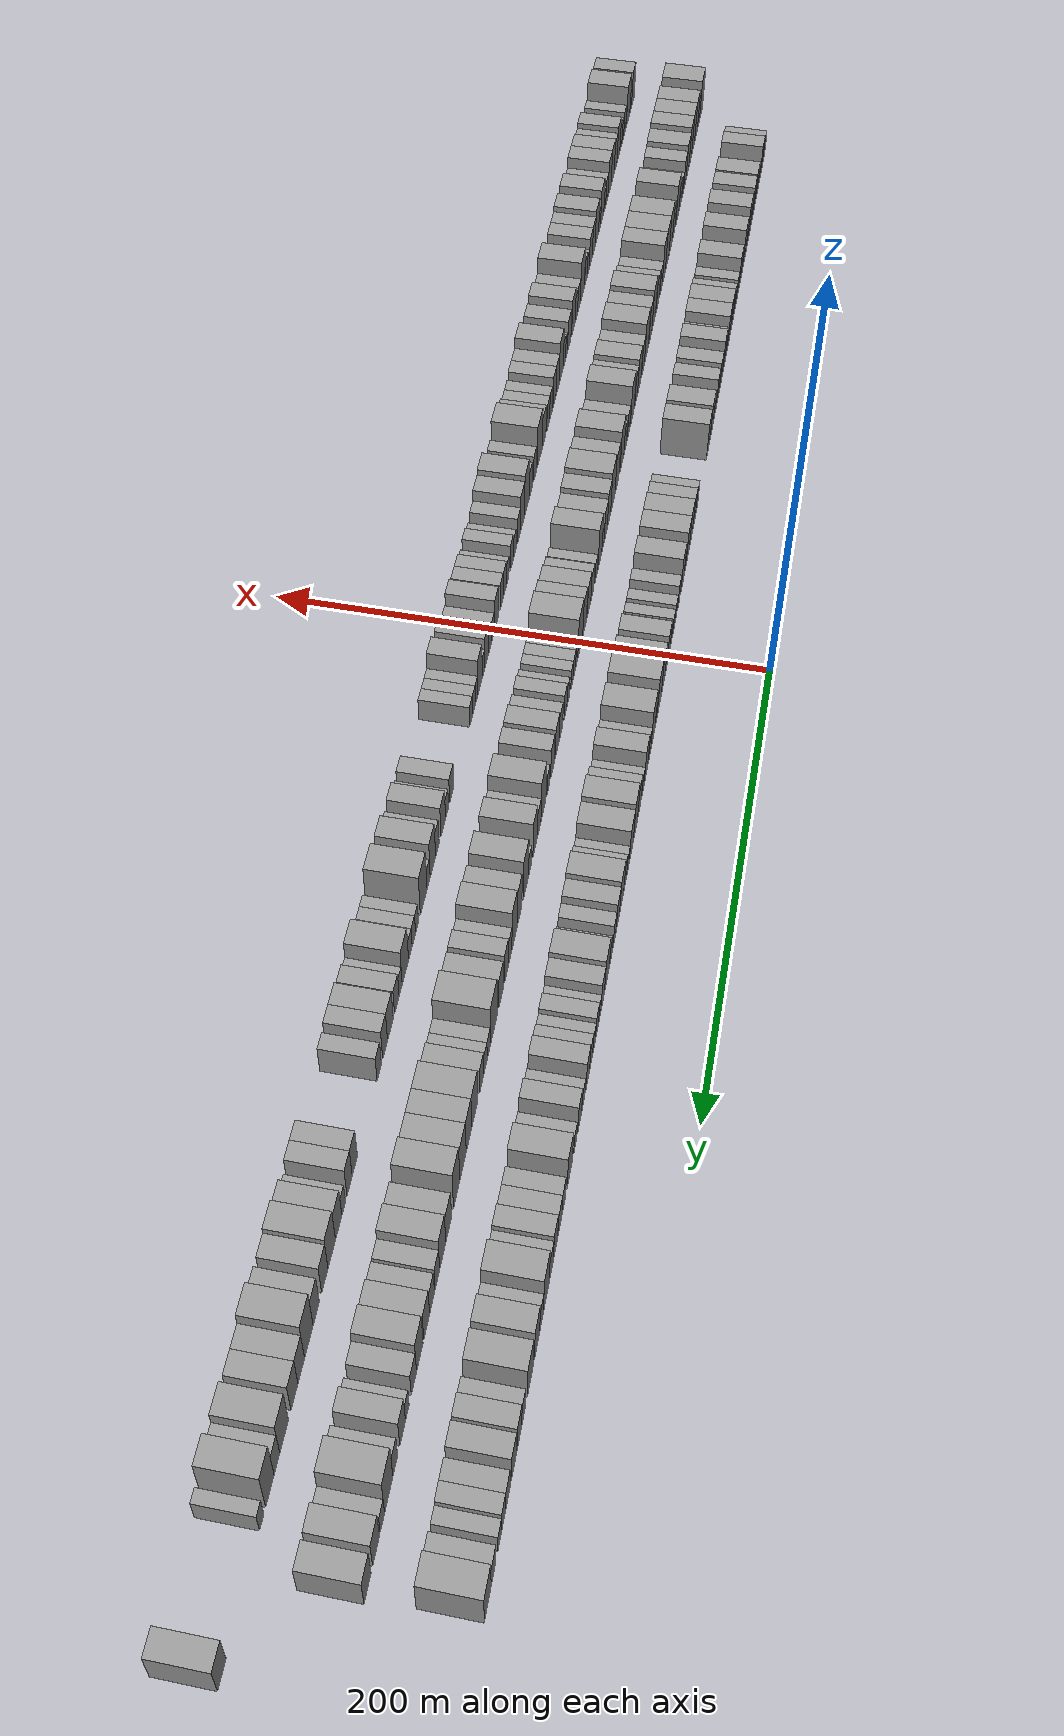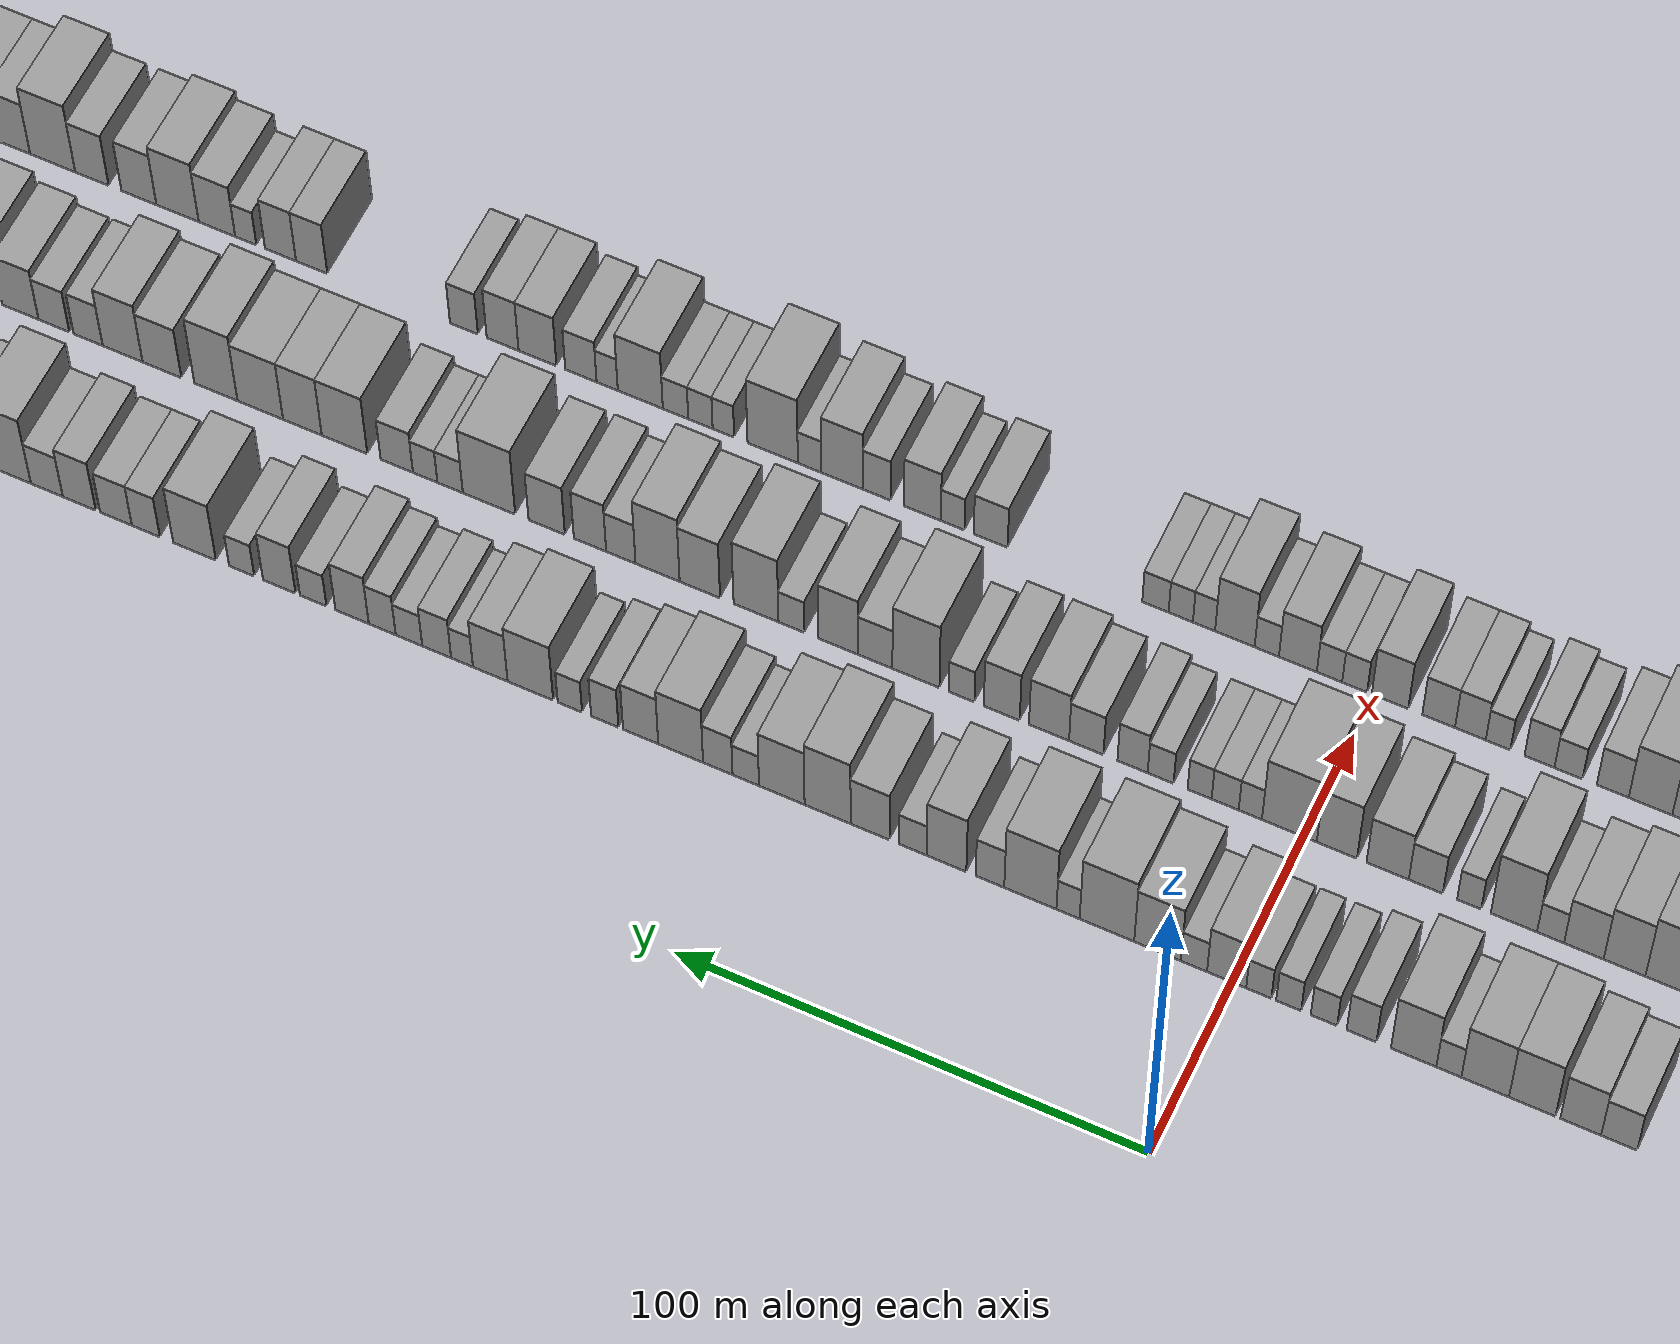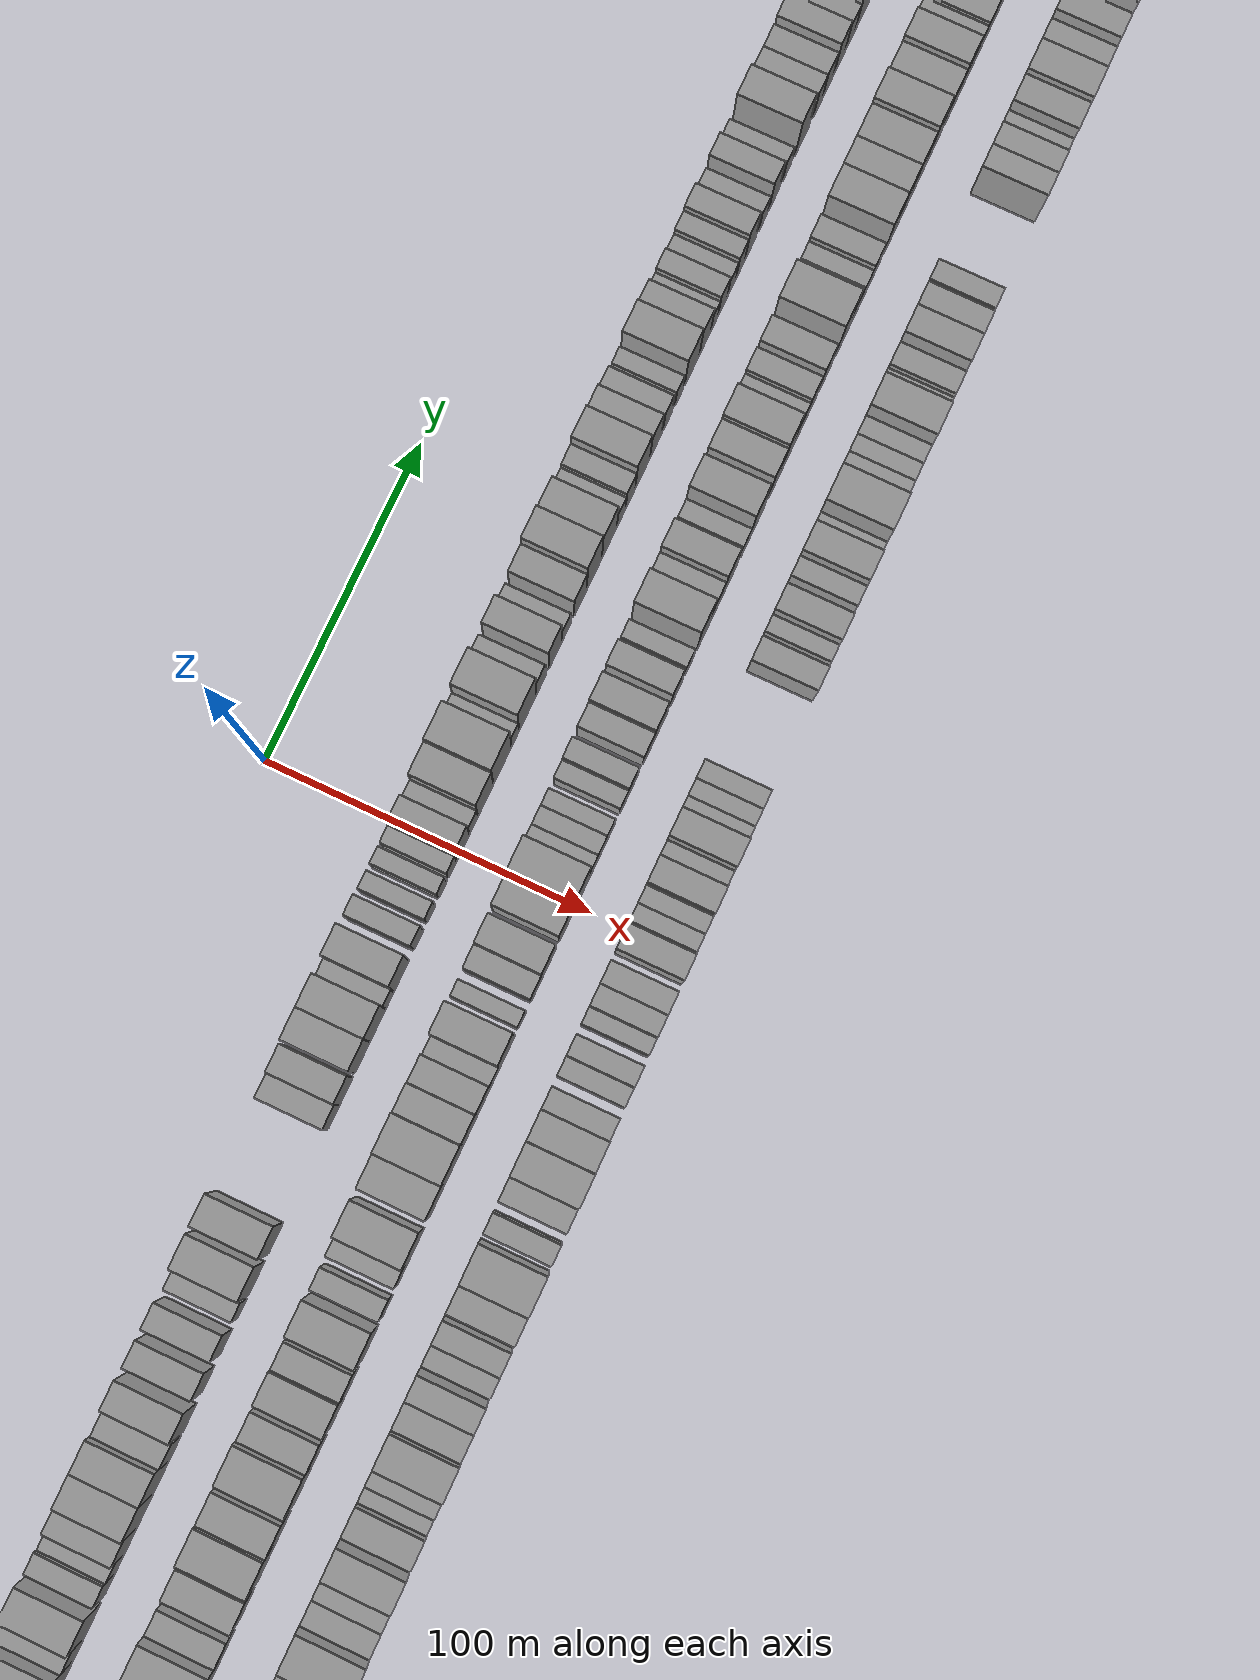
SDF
<sdf version="1.6">
 <world name="default">
  <scene>
   <sky><clouds><speed>12</speed></clouds></sky>
   <ambient>0.4 0.4 0.4 1</ambient>
   <background>0.7 0.7 0.7 1</background>
   <shadows>1</shadows>
  </scene>
  <gravity>0 0 -9.8066</gravity>
  <magnetic_field>6e-06 2.3e-05 -4.2e-05</magnetic_field>
  <physics default="0" name="default_physics" type="ode">
   <ode>
    <solver>
     <type>quick</type>
     <iters>10</iters>
     <sor>1.0</sor>
     <use_dynamic_moi_rescaling>0</use_dynamic_moi_rescaling>
    </solver>
    <constraints>
     <cfm>0</cfm>
     <erp>0.2</erp>
     <contact_max_correcting_vel>100</contact_max_correcting_vel>
     <contact_surface_layer>0.001</contact_surface_layer>
    </constraints>
   </ode>
   <max_step_size>0.004</max_step_size>
   <real_time_factor>1</real_time_factor>
   <real_time_update_rate>250</real_time_update_rate>
  </physics>
  <light name="sun" type="directional">
   <pose>0 0 10 0 0 0</pose>
   <diffuse>0.8 0.8 0.8 1</diffuse>
   <specular>0.2 0.2 0.2 1</specular>
   <attenuation>
    <range>1000</range>
    <constant>0.9</constant>
    <linear>0.01</linear>
    <quadratic>0.001</quadratic>
   </attenuation>
   <direction>-0.5 0.1 -0.9</direction>
  </light>
  <model name="building_1">
   <static>1</static>
   <pose>50.0000 -323.5235 0 0.000000 0.000000 0.000000</pose>
   <link name="link">
    <pose>0 0 6.00 0 0 0</pose>
    <collision name="collision"><geometry><box><size>20.0000 4.9844 12.0000</size></box></geometry></collision>
    <visual name="visual">
     <cast_shadows>0</cast_shadows>
     <geometry><box><size>20.0000 4.9844 12.0000</size></box></geometry>
     <material>
      <script>
       <uri>model://grey_wall/materials/scripts</uri>
       <uri>model://grey_wall/materials/textures</uri>
       <name>vrc/grey_wall</name>
      </script>
     </material>
    </visual>
   </link>
  </model>
  <model name="building_2">
   <static>1</static>
   <pose>50.0000 -316.8448 0 0.000000 0.000000 0.000000</pose>
   <link name="link">
    <pose>0 0 9.00 0 0 0</pose>
    <collision name="collision"><geometry><box><size>20.0000 8.3730 18.0000</size></box></geometry></collision>
    <visual name="visual">
     <cast_shadows>0</cast_shadows>
     <geometry><box><size>20.0000 8.3730 18.0000</size></box></geometry>
     <material>
      <script>
       <uri>model://grey_wall/materials/scripts</uri>
       <uri>model://grey_wall/materials/textures</uri>
       <name>vrc/grey_wall</name>
      </script>
     </material>
    </visual>
   </link>
  </model>
  <model name="building_3">
   <static>1</static>
   <pose>50.0000 -308.3304 0 0.000000 0.000000 0.000000</pose>
   <link name="link">
    <pose>0 0 10.50 0 0 0</pose>
    <collision name="collision"><geometry><box><size>20.0000 8.6558 21.0000</size></box></geometry></collision>
    <visual name="visual">
     <cast_shadows>0</cast_shadows>
     <geometry><box><size>20.0000 8.6558 21.0000</size></box></geometry>
     <material>
      <script>
       <uri>model://grey_wall/materials/scripts</uri>
       <uri>model://grey_wall/materials/textures</uri>
       <name>vrc/grey_wall</name>
      </script>
     </material>
    </visual>
   </link>
  </model>
  <model name="building_4">
   <static>1</static>
   <pose>50.0000 -301.5151 0 0.000000 0.000000 0.000000</pose>
   <link name="link">
    <pose>0 0 6.00 0 0 0</pose>
    <collision name="collision"><geometry><box><size>20.0000 4.9749 12.0000</size></box></geometry></collision>
    <visual name="visual">
     <cast_shadows>0</cast_shadows>
     <geometry><box><size>20.0000 4.9749 12.0000</size></box></geometry>
     <material>
      <script>
       <uri>model://grey_wall/materials/scripts</uri>
       <uri>model://grey_wall/materials/textures</uri>
       <name>vrc/grey_wall</name>
      </script>
     </material>
    </visual>
   </link>
  </model>
  <model name="building_5">
   <static>1</static>
   <pose>50.0000 -295.2361 0 0.000000 0.000000 0.000000</pose>
   <link name="link">
    <pose>0 0 6.00 0 0 0</pose>
    <collision name="collision"><geometry><box><size>20.0000 5.5831 12.0000</size></box></geometry></collision>
    <visual name="visual">
     <cast_shadows>0</cast_shadows>
     <geometry><box><size>20.0000 5.5831 12.0000</size></box></geometry>
     <material>
      <script>
       <uri>model://grey_wall/materials/scripts</uri>
       <uri>model://grey_wall/materials/textures</uri>
       <name>vrc/grey_wall</name>
      </script>
     </material>
    </visual>
   </link>
  </model>
  <model name="building_6">
   <static>1</static>
   <pose>50.0000 -287.4168 0 0.000000 0.000000 0.000000</pose>
   <link name="link">
    <pose>0 0 10.50 0 0 0</pose>
    <collision name="collision"><geometry><box><size>20.0000 10.0555 21.0000</size></box></geometry></collision>
    <visual name="visual">
     <cast_shadows>0</cast_shadows>
     <geometry><box><size>20.0000 10.0555 21.0000</size></box></geometry>
     <material>
      <script>
       <uri>model://grey_wall/materials/scripts</uri>
       <uri>model://grey_wall/materials/textures</uri>
       <name>vrc/grey_wall</name>
      </script>
     </material>
    </visual>
   </link>
  </model>
  <model name="building_7">
   <static>1</static>
   <pose>50.0000 -276.7406 0 0.000000 0.000000 0.000000</pose>
   <link name="link">
    <pose>0 0 10.50 0 0 0</pose>
    <collision name="collision"><geometry><box><size>20.0000 9.2968 21.0000</size></box></geometry></collision>
    <visual name="visual">
     <cast_shadows>0</cast_shadows>
     <geometry><box><size>20.0000 9.2968 21.0000</size></box></geometry>
     <material>
      <script>
       <uri>model://grey_wall/materials/scripts</uri>
       <uri>model://grey_wall/materials/textures</uri>
       <name>vrc/grey_wall</name>
      </script>
     </material>
    </visual>
   </link>
  </model>
  <model name="building_8">
   <static>1</static>
   <pose>50.0000 -267.5403 0 0.000000 0.000000 0.000000</pose>
   <link name="link">
    <pose>0 0 7.50 0 0 0</pose>
    <collision name="collision"><geometry><box><size>20.0000 7.1037 15.0000</size></box></geometry></collision>
    <visual name="visual">
     <cast_shadows>0</cast_shadows>
     <geometry><box><size>20.0000 7.1037 15.0000</size></box></geometry>
     <material>
      <script>
       <uri>model://grey_wall/materials/scripts</uri>
       <uri>model://grey_wall/materials/textures</uri>
       <name>vrc/grey_wall</name>
      </script>
     </material>
    </visual>
   </link>
  </model>
  <model name="building_9">
   <static>1</static>
   <pose>50.0000 -258.8711 0 0.000000 0.000000 0.000000</pose>
   <link name="link">
    <pose>0 0 12.00 0 0 0</pose>
    <collision name="collision"><geometry><box><size>20.0000 10.2348 24.0000</size></box></geometry></collision>
    <visual name="visual">
     <cast_shadows>0</cast_shadows>
     <geometry><box><size>20.0000 10.2348 24.0000</size></box></geometry>
     <material>
      <script>
       <uri>model://grey_wall/materials/scripts</uri>
       <uri>model://grey_wall/materials/textures</uri>
       <name>vrc/grey_wall</name>
      </script>
     </material>
    </visual>
   </link>
  </model>
  <model name="building_10">
   <static>1</static>
   <pose>50.0000 -250.3590 0 0.000000 0.000000 0.000000</pose>
   <link name="link">
    <pose>0 0 7.50 0 0 0</pose>
    <collision name="collision"><geometry><box><size>20.0000 6.7893 15.0000</size></box></geometry></collision>
    <visual name="visual">
     <cast_shadows>0</cast_shadows>
     <geometry><box><size>20.0000 6.7893 15.0000</size></box></geometry>
     <material>
      <script>
       <uri>model://grey_wall/materials/scripts</uri>
       <uri>model://grey_wall/materials/textures</uri>
       <name>vrc/grey_wall</name>
      </script>
     </material>
    </visual>
   </link>
  </model>
  <model name="building_11">
   <static>1</static>
   <pose>50.0000 -241.8645 0 0.000000 0.000000 0.000000</pose>
   <link name="link">
    <pose>0 0 12.00 0 0 0</pose>
    <collision name="collision"><geometry><box><size>20.0000 10.1996 24.0000</size></box></geometry></collision>
    <visual name="visual">
     <cast_shadows>0</cast_shadows>
     <geometry><box><size>20.0000 10.1996 24.0000</size></box></geometry>
     <material>
      <script>
       <uri>model://grey_wall/materials/scripts</uri>
       <uri>model://grey_wall/materials/textures</uri>
       <name>vrc/grey_wall</name>
      </script>
     </material>
    </visual>
   </link>
  </model>
  <model name="building_12">
   <static>1</static>
   <pose>50.0000 -233.6002 0 0.000000 0.000000 0.000000</pose>
   <link name="link">
    <pose>0 0 7.50 0 0 0</pose>
    <collision name="collision"><geometry><box><size>20.0000 6.3291 15.0000</size></box></geometry></collision>
    <visual name="visual">
     <cast_shadows>0</cast_shadows>
     <geometry><box><size>20.0000 6.3291 15.0000</size></box></geometry>
     <material>
      <script>
       <uri>model://grey_wall/materials/scripts</uri>
       <uri>model://grey_wall/materials/textures</uri>
       <name>vrc/grey_wall</name>
      </script>
     </material>
    </visual>
   </link>
  </model>
  <model name="building_13">
   <static>1</static>
   <pose>50.0000 -225.4754 0 0.000000 0.000000 0.000000</pose>
   <link name="link">
    <pose>0 0 10.50 0 0 0</pose>
    <collision name="collision"><geometry><box><size>20.0000 9.9203 21.0000</size></box></geometry></collision>
    <visual name="visual">
     <cast_shadows>0</cast_shadows>
     <geometry><box><size>20.0000 9.9203 21.0000</size></box></geometry>
     <material>
      <script>
       <uri>model://grey_wall/materials/scripts</uri>
       <uri>model://grey_wall/materials/textures</uri>
       <name>vrc/grey_wall</name>
      </script>
     </material>
    </visual>
   </link>
  </model>
  <model name="building_14">
   <static>1</static>
   <pose>50.0000 -215.4575 0 0.000000 0.000000 0.000000</pose>
   <link name="link">
    <pose>0 0 7.50 0 0 0</pose>
    <collision name="collision"><geometry><box><size>20.0000 6.1157 15.0000</size></box></geometry></collision>
    <visual name="visual">
     <cast_shadows>0</cast_shadows>
     <geometry><box><size>20.0000 6.1157 15.0000</size></box></geometry>
     <material>
      <script>
       <uri>model://grey_wall/materials/scripts</uri>
       <uri>model://grey_wall/materials/textures</uri>
       <name>vrc/grey_wall</name>
      </script>
     </material>
    </visual>
   </link>
  </model>
  <model name="building_15">
   <static>1</static>
   <pose>50.0000 -209.5871 0 0.000000 0.000000 0.000000</pose>
   <link name="link">
    <pose>0 0 6.00 0 0 0</pose>
    <collision name="collision"><geometry><box><size>20.0000 5.6250 12.0000</size></box></geometry></collision>
    <visual name="visual">
     <cast_shadows>0</cast_shadows>
     <geometry><box><size>20.0000 5.6250 12.0000</size></box></geometry>
     <material>
      <script>
       <uri>model://grey_wall/materials/scripts</uri>
       <uri>model://grey_wall/materials/textures</uri>
       <name>vrc/grey_wall</name>
      </script>
     </material>
    </visual>
   </link>
  </model>
  <model name="building_16">
   <static>1</static>
   <pose>50.0000 -203.0553 0 0.000000 0.000000 0.000000</pose>
   <link name="link">
    <pose>0 0 9.00 0 0 0</pose>
    <collision name="collision"><geometry><box><size>20.0000 7.4387 18.0000</size></box></geometry></collision>
    <visual name="visual">
     <cast_shadows>0</cast_shadows>
     <geometry><box><size>20.0000 7.4387 18.0000</size></box></geometry>
     <material>
      <script>
       <uri>model://grey_wall/materials/scripts</uri>
       <uri>model://grey_wall/materials/textures</uri>
       <name>vrc/grey_wall</name>
      </script>
     </material>
    </visual>
   </link>
  </model>
  <model name="building_17">
   <static>1</static>
   <pose>50.0000 -194.4742 0 0.000000 0.000000 0.000000</pose>
   <link name="link">
    <pose>0 0 10.50 0 0 0</pose>
    <collision name="collision"><geometry><box><size>20.0000 9.7235 21.0000</size></box></geometry></collision>
    <visual name="visual">
     <cast_shadows>0</cast_shadows>
     <geometry><box><size>20.0000 9.7235 21.0000</size></box></geometry>
     <material>
      <script>
       <uri>model://grey_wall/materials/scripts</uri>
       <uri>model://grey_wall/materials/textures</uri>
       <name>vrc/grey_wall</name>
      </script>
     </material>
    </visual>
   </link>
  </model>
  <model name="building_18">
   <static>1</static>
   <pose>50.0000 -184.9222 0 0.000000 0.000000 0.000000</pose>
   <link name="link">
    <pose>0 0 10.50 0 0 0</pose>
    <collision name="collision"><geometry><box><size>20.0000 9.3804 21.0000</size></box></geometry></collision>
    <visual name="visual">
     <cast_shadows>0</cast_shadows>
     <geometry><box><size>20.0000 9.3804 21.0000</size></box></geometry>
     <material>
      <script>
       <uri>model://grey_wall/materials/scripts</uri>
       <uri>model://grey_wall/materials/textures</uri>
       <name>vrc/grey_wall</name>
      </script>
     </material>
    </visual>
   </link>
  </model>
  <model name="building_19">
   <static>1</static>
   <pose>50.0000 -176.6971 0 0.000000 0.000000 0.000000</pose>
   <link name="link">
    <pose>0 0 7.50 0 0 0</pose>
    <collision name="collision"><geometry><box><size>20.0000 7.0700 15.0000</size></box></geometry></collision>
    <visual name="visual">
     <cast_shadows>0</cast_shadows>
     <geometry><box><size>20.0000 7.0700 15.0000</size></box></geometry>
     <material>
      <script>
       <uri>model://grey_wall/materials/scripts</uri>
       <uri>model://grey_wall/materials/textures</uri>
       <name>vrc/grey_wall</name>
      </script>
     </material>
    </visual>
   </link>
  </model>
  <model name="building_20">
   <static>1</static>
   <pose>50.0000 -167.8782 0 0.000000 0.000000 0.000000</pose>
   <link name="link">
    <pose>0 0 10.50 0 0 0</pose>
    <collision name="collision"><geometry><box><size>20.0000 8.5677 21.0000</size></box></geometry></collision>
    <visual name="visual">
     <cast_shadows>0</cast_shadows>
     <geometry><box><size>20.0000 8.5677 21.0000</size></box></geometry>
     <material>
      <script>
       <uri>model://grey_wall/materials/scripts</uri>
       <uri>model://grey_wall/materials/textures</uri>
       <name>vrc/grey_wall</name>
      </script>
     </material>
    </visual>
   </link>
  </model>
  <model name="building_21">
   <static>1</static>
   <pose>50.0000 -156.6761 0 0.000000 0.000000 0.000000</pose>
   <link name="link">
    <pose>0 0 9.00 0 0 0</pose>
    <collision name="collision"><geometry><box><size>20.0000 7.8365 18.0000</size></box></geometry></collision>
    <visual name="visual">
     <cast_shadows>0</cast_shadows>
     <geometry><box><size>20.0000 7.8365 18.0000</size></box></geometry>
     <material>
      <script>
       <uri>model://grey_wall/materials/scripts</uri>
       <uri>model://grey_wall/materials/textures</uri>
       <name>vrc/grey_wall</name>
      </script>
     </material>
    </visual>
   </link>
  </model>
  <model name="building_22">
   <static>1</static>
   <pose>50.0000 -145.9216 0 0.000000 0.000000 0.000000</pose>
   <link name="link">
    <pose>0 0 9.00 0 0 0</pose>
    <collision name="collision"><geometry><box><size>20.0000 7.6724 18.0000</size></box></geometry></collision>
    <visual name="visual">
     <cast_shadows>0</cast_shadows>
     <geometry><box><size>20.0000 7.6724 18.0000</size></box></geometry>
     <material>
      <script>
       <uri>model://grey_wall/materials/scripts</uri>
       <uri>model://grey_wall/materials/textures</uri>
       <name>vrc/grey_wall</name>
      </script>
     </material>
    </visual>
   </link>
  </model>
  <model name="building_23">
   <static>1</static>
   <pose>50.0000 -136.2911 0 0.000000 0.000000 0.000000</pose>
   <link name="link">
    <pose>0 0 6.00 0 0 0</pose>
    <collision name="collision"><geometry><box><size>20.0000 5.5886 12.0000</size></box></geometry></collision>
    <visual name="visual">
     <cast_shadows>0</cast_shadows>
     <geometry><box><size>20.0000 5.5886 12.0000</size></box></geometry>
     <material>
      <script>
       <uri>model://grey_wall/materials/scripts</uri>
       <uri>model://grey_wall/materials/textures</uri>
       <name>vrc/grey_wall</name>
      </script>
     </material>
    </visual>
   </link>
  </model>
  <model name="building_24">
   <static>1</static>
   <pose>50.0000 -127.4564 0 0.000000 0.000000 0.000000</pose>
   <link name="link">
    <pose>0 0 10.50 0 0 0</pose>
    <collision name="collision"><geometry><box><size>20.0000 10.0809 21.0000</size></box></geometry></collision>
    <visual name="visual">
     <cast_shadows>0</cast_shadows>
     <geometry><box><size>20.0000 10.0809 21.0000</size></box></geometry>
     <material>
      <script>
       <uri>model://grey_wall/materials/scripts</uri>
       <uri>model://grey_wall/materials/textures</uri>
       <name>vrc/grey_wall</name>
      </script>
     </material>
    </visual>
   </link>
  </model>
  <model name="building_25">
   <static>1</static>
   <pose>50.0000 -115.7088 0 0.000000 0.000000 0.000000</pose>
   <link name="link">
    <pose>0 0 10.50 0 0 0</pose>
    <collision name="collision"><geometry><box><size>20.0000 9.4143 21.0000</size></box></geometry></collision>
    <visual name="visual">
     <cast_shadows>0</cast_shadows>
     <geometry><box><size>20.0000 9.4143 21.0000</size></box></geometry>
     <material>
      <script>
       <uri>model://grey_wall/materials/scripts</uri>
       <uri>model://grey_wall/materials/textures</uri>
       <name>vrc/grey_wall</name>
      </script>
     </material>
    </visual>
   </link>
  </model>
  <model name="building_26">
   <static>1</static>
   <pose>50.0000 -79.9484 0 0.000000 0.000000 0.000000</pose>
   <link name="link">
    <pose>0 0 7.50 0 0 0</pose>
    <collision name="collision"><geometry><box><size>20.0000 7.3688 15.0000</size></box></geometry></collision>
    <visual name="visual">
     <cast_shadows>0</cast_shadows>
     <geometry><box><size>20.0000 7.3688 15.0000</size></box></geometry>
     <material>
      <script>
       <uri>model://grey_wall/materials/scripts</uri>
       <uri>model://grey_wall/materials/textures</uri>
       <name>vrc/grey_wall</name>
      </script>
     </material>
    </visual>
   </link>
  </model>
  <model name="building_27">
   <static>1</static>
   <pose>50.0000 -72.0861 0 0.000000 0.000000 0.000000</pose>
   <link name="link">
    <pose>0 0 9.00 0 0 0</pose>
    <collision name="collision"><geometry><box><size>20.0000 8.3559 18.0000</size></box></geometry></collision>
    <visual name="visual">
     <cast_shadows>0</cast_shadows>
     <geometry><box><size>20.0000 8.3559 18.0000</size></box></geometry>
     <material>
      <script>
       <uri>model://grey_wall/materials/scripts</uri>
       <uri>model://grey_wall/materials/textures</uri>
       <name>vrc/grey_wall</name>
      </script>
     </material>
    </visual>
   </link>
  </model>
  <model name="building_28">
   <static>1</static>
   <pose>50.0000 -62.1377 0 0.000000 0.000000 0.000000</pose>
   <link name="link">
    <pose>0 0 10.50 0 0 0</pose>
    <collision name="collision"><geometry><box><size>20.0000 9.5409 21.0000</size></box></geometry></collision>
    <visual name="visual">
     <cast_shadows>0</cast_shadows>
     <geometry><box><size>20.0000 9.5409 21.0000</size></box></geometry>
     <material>
      <script>
       <uri>model://grey_wall/materials/scripts</uri>
       <uri>model://grey_wall/materials/textures</uri>
       <name>vrc/grey_wall</name>
      </script>
     </material>
    </visual>
   </link>
  </model>
  <model name="building_29">
   <static>1</static>
   <pose>50.0000 -52.4496 0 0.000000 0.000000 0.000000</pose>
   <link name="link">
    <pose>0 0 10.50 0 0 0</pose>
    <collision name="collision"><geometry><box><size>20.0000 9.8351 21.0000</size></box></geometry></collision>
    <visual name="visual">
     <cast_shadows>0</cast_shadows>
     <geometry><box><size>20.0000 9.8351 21.0000</size></box></geometry>
     <material>
      <script>
       <uri>model://grey_wall/materials/scripts</uri>
       <uri>model://grey_wall/materials/textures</uri>
       <name>vrc/grey_wall</name>
      </script>
     </material>
    </visual>
   </link>
  </model>
  <model name="building_30">
   <static>1</static>
   <pose>50.0000 -44.9440 0 0.000000 0.000000 0.000000</pose>
   <link name="link">
    <pose>0 0 6.00 0 0 0</pose>
    <collision name="collision"><geometry><box><size>20.0000 5.1762 12.0000</size></box></geometry></collision>
    <visual name="visual">
     <cast_shadows>0</cast_shadows>
     <geometry><box><size>20.0000 5.1762 12.0000</size></box></geometry>
     <material>
      <script>
       <uri>model://grey_wall/materials/scripts</uri>
       <uri>model://grey_wall/materials/textures</uri>
       <name>vrc/grey_wall</name>
      </script>
     </material>
    </visual>
   </link>
  </model>
  <model name="building_31">
   <static>1</static>
   <pose>50.0000 -37.6500 0 0.000000 0.000000 0.000000</pose>
   <link name="link">
    <pose>0 0 10.50 0 0 0</pose>
    <collision name="collision"><geometry><box><size>20.0000 9.4118 21.0000</size></box></geometry></collision>
    <visual name="visual">
     <cast_shadows>0</cast_shadows>
     <geometry><box><size>20.0000 9.4118 21.0000</size></box></geometry>
     <material>
      <script>
       <uri>model://grey_wall/materials/scripts</uri>
       <uri>model://grey_wall/materials/textures</uri>
       <name>vrc/grey_wall</name>
      </script>
     </material>
    </visual>
   </link>
  </model>
  <model name="building_32">
   <static>1</static>
   <pose>50.0000 -26.8472 0 0.000000 0.000000 0.000000</pose>
   <link name="link">
    <pose>0 0 7.50 0 0 0</pose>
    <collision name="collision"><geometry><box><size>20.0000 6.1937 15.0000</size></box></geometry></collision>
    <visual name="visual">
     <cast_shadows>0</cast_shadows>
     <geometry><box><size>20.0000 6.1937 15.0000</size></box></geometry>
     <material>
      <script>
       <uri>model://grey_wall/materials/scripts</uri>
       <uri>model://grey_wall/materials/textures</uri>
       <name>vrc/grey_wall</name>
      </script>
     </material>
    </visual>
   </link>
  </model>
  <model name="building_33">
   <static>1</static>
   <pose>50.0000 -19.0019 0 0.000000 0.000000 0.000000</pose>
   <link name="link">
    <pose>0 0 6.00 0 0 0</pose>
    <collision name="collision"><geometry><box><size>20.0000 5.4968 12.0000</size></box></geometry></collision>
    <visual name="visual">
     <cast_shadows>0</cast_shadows>
     <geometry><box><size>20.0000 5.4968 12.0000</size></box></geometry>
     <material>
      <script>
       <uri>model://grey_wall/materials/scripts</uri>
       <uri>model://grey_wall/materials/textures</uri>
       <name>vrc/grey_wall</name>
      </script>
     </material>
    </visual>
   </link>
  </model>
  <model name="building_34">
   <static>1</static>
   <pose>50.0000 -11.6341 0 0.000000 0.000000 0.000000</pose>
   <link name="link">
    <pose>0 0 6.00 0 0 0</pose>
    <collision name="collision"><geometry><box><size>20.0000 5.2390 12.0000</size></box></geometry></collision>
    <visual name="visual">
     <cast_shadows>0</cast_shadows>
     <geometry><box><size>20.0000 5.2390 12.0000</size></box></geometry>
     <material>
      <script>
       <uri>model://grey_wall/materials/scripts</uri>
       <uri>model://grey_wall/materials/textures</uri>
       <name>vrc/grey_wall</name>
      </script>
     </material>
    </visual>
   </link>
  </model>
  <model name="building_35">
   <static>1</static>
   <pose>50.0000 -5.3701 0 0.000000 0.000000 0.000000</pose>
   <link name="link">
    <pose>0 0 6.00 0 0 0</pose>
    <collision name="collision"><geometry><box><size>20.0000 5.2889 12.0000</size></box></geometry></collision>
    <visual name="visual">
     <cast_shadows>0</cast_shadows>
     <geometry><box><size>20.0000 5.2889 12.0000</size></box></geometry>
     <material>
      <script>
       <uri>model://grey_wall/materials/scripts</uri>
       <uri>model://grey_wall/materials/textures</uri>
       <name>vrc/grey_wall</name>
      </script>
     </material>
    </visual>
   </link>
  </model>
  <model name="building_36">
   <static>1</static>
   <pose>50.0000 1.3845 0 0.000000 0.000000 0.000000</pose>
   <link name="link">
    <pose>0 0 9.00 0 0 0</pose>
    <collision name="collision"><geometry><box><size>20.0000 8.2204 18.0000</size></box></geometry></collision>
    <visual name="visual">
     <cast_shadows>0</cast_shadows>
     <geometry><box><size>20.0000 8.2204 18.0000</size></box></geometry>
     <material>
      <script>
       <uri>model://grey_wall/materials/scripts</uri>
       <uri>model://grey_wall/materials/textures</uri>
       <name>vrc/grey_wall</name>
      </script>
     </material>
    </visual>
   </link>
  </model>
  <model name="building_37">
   <static>1</static>
   <pose>50.0000 8.2533 0 0.000000 0.000000 0.000000</pose>
   <link name="link">
    <pose>0 0 6.00 0 0 0</pose>
    <collision name="collision"><geometry><box><size>20.0000 5.5172 12.0000</size></box></geometry></collision>
    <visual name="visual">
     <cast_shadows>0</cast_shadows>
     <geometry><box><size>20.0000 5.5172 12.0000</size></box></geometry>
     <material>
      <script>
       <uri>model://grey_wall/materials/scripts</uri>
       <uri>model://grey_wall/materials/textures</uri>
       <name>vrc/grey_wall</name>
      </script>
     </material>
    </visual>
   </link>
  </model>
  <model name="building_38">
   <static>1</static>
   <pose>50.0000 15.9402 0 0.000000 0.000000 0.000000</pose>
   <link name="link">
    <pose>0 0 10.50 0 0 0</pose>
    <collision name="collision"><geometry><box><size>20.0000 9.8565 21.0000</size></box></geometry></collision>
    <visual name="visual">
     <cast_shadows>0</cast_shadows>
     <geometry><box><size>20.0000 9.8565 21.0000</size></box></geometry>
     <material>
      <script>
       <uri>model://grey_wall/materials/scripts</uri>
       <uri>model://grey_wall/materials/textures</uri>
       <name>vrc/grey_wall</name>
      </script>
     </material>
    </visual>
   </link>
  </model>
  <model name="building_39">
   <static>1</static>
   <pose>50.0000 26.6583 0 0.000000 0.000000 0.000000</pose>
   <link name="link">
    <pose>0 0 12.00 0 0 0</pose>
    <collision name="collision"><geometry><box><size>20.0000 11.5798 24.0000</size></box></geometry></collision>
    <visual name="visual">
     <cast_shadows>0</cast_shadows>
     <geometry><box><size>20.0000 11.5798 24.0000</size></box></geometry>
     <material>
      <script>
       <uri>model://grey_wall/materials/scripts</uri>
       <uri>model://grey_wall/materials/textures</uri>
       <name>vrc/grey_wall</name>
      </script>
     </material>
    </visual>
   </link>
  </model>
  <model name="building_40">
   <static>1</static>
   <pose>50.0000 34.9104 0 0.000000 0.000000 0.000000</pose>
   <link name="link">
    <pose>0 0 6.00 0 0 0</pose>
    <collision name="collision"><geometry><box><size>20.0000 4.9244 12.0000</size></box></geometry></collision>
    <visual name="visual">
     <cast_shadows>0</cast_shadows>
     <geometry><box><size>20.0000 4.9244 12.0000</size></box></geometry>
     <material>
      <script>
       <uri>model://grey_wall/materials/scripts</uri>
       <uri>model://grey_wall/materials/textures</uri>
       <name>vrc/grey_wall</name>
      </script>
     </material>
    </visual>
   </link>
  </model>
  <model name="building_41">
   <static>1</static>
   <pose>50.0000 42.9367 0 0.000000 0.000000 0.000000</pose>
   <link name="link">
    <pose>0 0 12.00 0 0 0</pose>
    <collision name="collision"><geometry><box><size>20.0000 11.1283 24.0000</size></box></geometry></collision>
    <visual name="visual">
     <cast_shadows>0</cast_shadows>
     <geometry><box><size>20.0000 11.1283 24.0000</size></box></geometry>
     <material>
      <script>
       <uri>model://grey_wall/materials/scripts</uri>
       <uri>model://grey_wall/materials/textures</uri>
       <name>vrc/grey_wall</name>
      </script>
     </material>
    </visual>
   </link>
  </model>
  <model name="building_42">
   <static>1</static>
   <pose>50.0000 51.5553 0 0.000000 0.000000 0.000000</pose>
   <link name="link">
    <pose>0 0 7.50 0 0 0</pose>
    <collision name="collision"><geometry><box><size>20.0000 6.1088 15.0000</size></box></geometry></collision>
    <visual name="visual">
     <cast_shadows>0</cast_shadows>
     <geometry><box><size>20.0000 6.1088 15.0000</size></box></geometry>
     <material>
      <script>
       <uri>model://grey_wall/materials/scripts</uri>
       <uri>model://grey_wall/materials/textures</uri>
       <name>vrc/grey_wall</name>
      </script>
     </material>
    </visual>
   </link>
  </model>
  <model name="building_43">
   <static>1</static>
   <pose>50.0000 60.8794 0 0.000000 0.000000 0.000000</pose>
   <link name="link">
    <pose>0 0 10.50 0 0 0</pose>
    <collision name="collision"><geometry><box><size>20.0000 8.5394 21.0000</size></box></geometry></collision>
    <visual name="visual">
     <cast_shadows>0</cast_shadows>
     <geometry><box><size>20.0000 8.5394 21.0000</size></box></geometry>
     <material>
      <script>
       <uri>model://grey_wall/materials/scripts</uri>
       <uri>model://grey_wall/materials/textures</uri>
       <name>vrc/grey_wall</name>
      </script>
     </material>
    </visual>
   </link>
  </model>
  <model name="building_44">
   <static>1</static>
   <pose>50.0000 68.1219 0 0.000000 0.000000 0.000000</pose>
   <link name="link">
    <pose>0 0 6.00 0 0 0</pose>
    <collision name="collision"><geometry><box><size>20.0000 5.9457 12.0000</size></box></geometry></collision>
    <visual name="visual">
     <cast_shadows>0</cast_shadows>
     <geometry><box><size>20.0000 5.9457 12.0000</size></box></geometry>
     <material>
      <script>
       <uri>model://grey_wall/materials/scripts</uri>
       <uri>model://grey_wall/materials/textures</uri>
       <name>vrc/grey_wall</name>
      </script>
     </material>
    </visual>
   </link>
  </model>
  <model name="building_45">
   <static>1</static>
   <pose>50.0000 77.2916 0 0.000000 0.000000 0.000000</pose>
   <link name="link">
    <pose>0 0 9.00 0 0 0</pose>
    <collision name="collision"><geometry><box><size>20.0000 8.3937 18.0000</size></box></geometry></collision>
    <visual name="visual">
     <cast_shadows>0</cast_shadows>
     <geometry><box><size>20.0000 8.3937 18.0000</size></box></geometry>
     <material>
      <script>
       <uri>model://grey_wall/materials/scripts</uri>
       <uri>model://grey_wall/materials/textures</uri>
       <name>vrc/grey_wall</name>
      </script>
     </material>
    </visual>
   </link>
  </model>
  <model name="building_46">
   <static>1</static>
   <pose>50.0000 86.4690 0 0.000000 0.000000 0.000000</pose>
   <link name="link">
    <pose>0 0 12.00 0 0 0</pose>
    <collision name="collision"><geometry><box><size>20.0000 9.9612 24.0000</size></box></geometry></collision>
    <visual name="visual">
     <cast_shadows>0</cast_shadows>
     <geometry><box><size>20.0000 9.9612 24.0000</size></box></geometry>
     <material>
      <script>
       <uri>model://grey_wall/materials/scripts</uri>
       <uri>model://grey_wall/materials/textures</uri>
       <name>vrc/grey_wall</name>
      </script>
     </material>
    </visual>
   </link>
  </model>
  <model name="building_47">
   <static>1</static>
   <pose>50.0000 96.3936 0 0.000000 0.000000 0.000000</pose>
   <link name="link">
    <pose>0 0 10.50 0 0 0</pose>
    <collision name="collision"><geometry><box><size>20.0000 9.8879 21.0000</size></box></geometry></collision>
    <visual name="visual">
     <cast_shadows>0</cast_shadows>
     <geometry><box><size>20.0000 9.8879 21.0000</size></box></geometry>
     <material>
      <script>
       <uri>model://grey_wall/materials/scripts</uri>
       <uri>model://grey_wall/materials/textures</uri>
       <name>vrc/grey_wall</name>
      </script>
     </material>
    </visual>
   </link>
  </model>
  <model name="building_48">
   <static>1</static>
   <pose>50.0000 104.2200 0 0.000000 0.000000 0.000000</pose>
   <link name="link">
    <pose>0 0 6.00 0 0 0</pose>
    <collision name="collision"><geometry><box><size>20.0000 5.7649 12.0000</size></box></geometry></collision>
    <visual name="visual">
     <cast_shadows>0</cast_shadows>
     <geometry><box><size>20.0000 5.7649 12.0000</size></box></geometry>
     <material>
      <script>
       <uri>model://grey_wall/materials/scripts</uri>
       <uri>model://grey_wall/materials/textures</uri>
       <name>vrc/grey_wall</name>
      </script>
     </material>
    </visual>
   </link>
  </model>
  <model name="building_49">
   <static>1</static>
   <pose>50.0000 110.3169 0 0.000000 0.000000 0.000000</pose>
   <link name="link">
    <pose>0 0 7.50 0 0 0</pose>
    <collision name="collision"><geometry><box><size>20.0000 6.4288 15.0000</size></box></geometry></collision>
    <visual name="visual">
     <cast_shadows>0</cast_shadows>
     <geometry><box><size>20.0000 6.4288 15.0000</size></box></geometry>
     <material>
      <script>
       <uri>model://grey_wall/materials/scripts</uri>
       <uri>model://grey_wall/materials/textures</uri>
       <name>vrc/grey_wall</name>
      </script>
     </material>
    </visual>
   </link>
  </model>
  <model name="building_50">
   <static>1</static>
   <pose>50.0000 118.4352 0 0.000000 0.000000 0.000000</pose>
   <link name="link">
    <pose>0 0 10.50 0 0 0</pose>
    <collision name="collision"><geometry><box><size>20.0000 9.8078 21.0000</size></box></geometry></collision>
    <visual name="visual">
     <cast_shadows>0</cast_shadows>
     <geometry><box><size>20.0000 9.8078 21.0000</size></box></geometry>
     <material>
      <script>
       <uri>model://grey_wall/materials/scripts</uri>
       <uri>model://grey_wall/materials/textures</uri>
       <name>vrc/grey_wall</name>
      </script>
     </material>
    </visual>
   </link>
  </model>
  <model name="building_51">
   <static>1</static>
   <pose>50.0000 127.1973 0 0.000000 0.000000 0.000000</pose>
   <link name="link">
    <pose>0 0 9.00 0 0 0</pose>
    <collision name="collision"><geometry><box><size>20.0000 7.7165 18.0000</size></box></geometry></collision>
    <visual name="visual">
     <cast_shadows>0</cast_shadows>
     <geometry><box><size>20.0000 7.7165 18.0000</size></box></geometry>
     <material>
      <script>
       <uri>model://grey_wall/materials/scripts</uri>
       <uri>model://grey_wall/materials/textures</uri>
       <name>vrc/grey_wall</name>
      </script>
     </material>
    </visual>
   </link>
  </model>
  <model name="building_52">
   <static>1</static>
   <pose>50.0000 135.0569 0 0.000000 0.000000 0.000000</pose>
   <link name="link">
    <pose>0 0 7.50 0 0 0</pose>
    <collision name="collision"><geometry><box><size>20.0000 6.0026 15.0000</size></box></geometry></collision>
    <visual name="visual">
     <cast_shadows>0</cast_shadows>
     <geometry><box><size>20.0000 6.0026 15.0000</size></box></geometry>
     <material>
      <script>
       <uri>model://grey_wall/materials/scripts</uri>
       <uri>model://grey_wall/materials/textures</uri>
       <name>vrc/grey_wall</name>
      </script>
     </material>
    </visual>
   </link>
  </model>
  <model name="building_53">
   <static>1</static>
   <pose>50.0000 142.7467 0 0.000000 0.000000 0.000000</pose>
   <link name="link">
    <pose>0 0 6.00 0 0 0</pose>
    <collision name="collision"><geometry><box><size>20.0000 5.3771 12.0000</size></box></geometry></collision>
    <visual name="visual">
     <cast_shadows>0</cast_shadows>
     <geometry><box><size>20.0000 5.3771 12.0000</size></box></geometry>
     <material>
      <script>
       <uri>model://grey_wall/materials/scripts</uri>
       <uri>model://grey_wall/materials/textures</uri>
       <name>vrc/grey_wall</name>
      </script>
     </material>
    </visual>
   </link>
  </model>
  <model name="building_54">
   <static>1</static>
   <pose>50.0000 151.4809 0 0.000000 0.000000 0.000000</pose>
   <link name="link">
    <pose>0 0 10.50 0 0 0</pose>
    <collision name="collision"><geometry><box><size>20.0000 10.0912 21.0000</size></box></geometry></collision>
    <visual name="visual">
     <cast_shadows>0</cast_shadows>
     <geometry><box><size>20.0000 10.0912 21.0000</size></box></geometry>
     <material>
      <script>
       <uri>model://grey_wall/materials/scripts</uri>
       <uri>model://grey_wall/materials/textures</uri>
       <name>vrc/grey_wall</name>
      </script>
     </material>
    </visual>
   </link>
  </model>
  <model name="building_55">
   <static>1</static>
   <pose>50.0000 160.3625 0 0.000000 0.000000 0.000000</pose>
   <link name="link">
    <pose>0 0 9.00 0 0 0</pose>
    <collision name="collision"><geometry><box><size>20.0000 7.6720 18.0000</size></box></geometry></collision>
    <visual name="visual">
     <cast_shadows>0</cast_shadows>
     <geometry><box><size>20.0000 7.6720 18.0000</size></box></geometry>
     <material>
      <script>
       <uri>model://grey_wall/materials/scripts</uri>
       <uri>model://grey_wall/materials/textures</uri>
       <name>vrc/grey_wall</name>
      </script>
     </material>
    </visual>
   </link>
  </model>
  <model name="building_56">
   <static>1</static>
   <pose>50.0000 166.6195 0 0.000000 0.000000 0.000000</pose>
   <link name="link">
    <pose>0 0 6.00 0 0 0</pose>
    <collision name="collision"><geometry><box><size>20.0000 4.8420 12.0000</size></box></geometry></collision>
    <visual name="visual">
     <cast_shadows>0</cast_shadows>
     <geometry><box><size>20.0000 4.8420 12.0000</size></box></geometry>
     <material>
      <script>
       <uri>model://grey_wall/materials/scripts</uri>
       <uri>model://grey_wall/materials/textures</uri>
       <name>vrc/grey_wall</name>
      </script>
     </material>
    </visual>
   </link>
  </model>
  <model name="building_57">
   <static>1</static>
   <pose>50.0000 172.2612 0 0.000000 0.000000 0.000000</pose>
   <link name="link">
    <pose>0 0 7.50 0 0 0</pose>
    <collision name="collision"><geometry><box><size>20.0000 6.4413 15.0000</size></box></geometry></collision>
    <visual name="visual">
     <cast_shadows>0</cast_shadows>
     <geometry><box><size>20.0000 6.4413 15.0000</size></box></geometry>
     <material>
      <script>
       <uri>model://grey_wall/materials/scripts</uri>
       <uri>model://grey_wall/materials/textures</uri>
       <name>vrc/grey_wall</name>
      </script>
     </material>
    </visual>
   </link>
  </model>
  <model name="building_58">
   <static>1</static>
   <pose>50.0000 178.4415 0 0.000000 0.000000 0.000000</pose>
   <link name="link">
    <pose>0 0 6.00 0 0 0</pose>
    <collision name="collision"><geometry><box><size>20.0000 5.9194 12.0000</size></box></geometry></collision>
    <visual name="visual">
     <cast_shadows>0</cast_shadows>
     <geometry><box><size>20.0000 5.9194 12.0000</size></box></geometry>
     <material>
      <script>
       <uri>model://grey_wall/materials/scripts</uri>
       <uri>model://grey_wall/materials/textures</uri>
       <name>vrc/grey_wall</name>
      </script>
     </material>
    </visual>
   </link>
  </model>
  <model name="building_59">
   <static>1</static>
   <pose>50.0000 184.4137 0 0.000000 0.000000 0.000000</pose>
   <link name="link">
    <pose>0 0 7.50 0 0 0</pose>
    <collision name="collision"><geometry><box><size>20.0000 6.0249 15.0000</size></box></geometry></collision>
    <visual name="visual">
     <cast_shadows>0</cast_shadows>
     <geometry><box><size>20.0000 6.0249 15.0000</size></box></geometry>
     <material>
      <script>
       <uri>model://grey_wall/materials/scripts</uri>
       <uri>model://grey_wall/materials/textures</uri>
       <name>vrc/grey_wall</name>
      </script>
     </material>
    </visual>
   </link>
  </model>
  <model name="building_60">
   <static>1</static>
   <pose>50.0000 191.1660 0 0.000000 0.000000 0.000000</pose>
   <link name="link">
    <pose>0 0 9.00 0 0 0</pose>
    <collision name="collision"><geometry><box><size>20.0000 7.4796 18.0000</size></box></geometry></collision>
    <visual name="visual">
     <cast_shadows>0</cast_shadows>
     <geometry><box><size>20.0000 7.4796 18.0000</size></box></geometry>
     <material>
      <script>
       <uri>model://grey_wall/materials/scripts</uri>
       <uri>model://grey_wall/materials/textures</uri>
       <name>vrc/grey_wall</name>
      </script>
     </material>
    </visual>
   </link>
  </model>
  <model name="building_61">
   <static>1</static>
   <pose>50.0000 199.8842 0 0.000000 0.000000 0.000000</pose>
   <link name="link">
    <pose>0 0 6.00 0 0 0</pose>
    <collision name="collision"><geometry><box><size>20.0000 5.9568 12.0000</size></box></geometry></collision>
    <visual name="visual">
     <cast_shadows>0</cast_shadows>
     <geometry><box><size>20.0000 5.9568 12.0000</size></box></geometry>
     <material>
      <script>
       <uri>model://grey_wall/materials/scripts</uri>
       <uri>model://grey_wall/materials/textures</uri>
       <name>vrc/grey_wall</name>
      </script>
     </material>
    </visual>
   </link>
  </model>
  <model name="building_62">
   <static>1</static>
   <pose>50.0000 207.5187 0 0.000000 0.000000 0.000000</pose>
   <link name="link">
    <pose>0 0 9.00 0 0 0</pose>
    <collision name="collision"><geometry><box><size>20.0000 7.3122 18.0000</size></box></geometry></collision>
    <visual name="visual">
     <cast_shadows>0</cast_shadows>
     <geometry><box><size>20.0000 7.3122 18.0000</size></box></geometry>
     <material>
      <script>
       <uri>model://grey_wall/materials/scripts</uri>
       <uri>model://grey_wall/materials/textures</uri>
       <name>vrc/grey_wall</name>
      </script>
     </material>
    </visual>
   </link>
  </model>
  <model name="building_63">
   <static>1</static>
   <pose>50.0000 216.0073 0 0.000000 0.000000 0.000000</pose>
   <link name="link">
    <pose>0 0 6.00 0 0 0</pose>
    <collision name="collision"><geometry><box><size>20.0000 5.6650 12.0000</size></box></geometry></collision>
    <visual name="visual">
     <cast_shadows>0</cast_shadows>
     <geometry><box><size>20.0000 5.6650 12.0000</size></box></geometry>
     <material>
      <script>
       <uri>model://grey_wall/materials/scripts</uri>
       <uri>model://grey_wall/materials/textures</uri>
       <name>vrc/grey_wall</name>
      </script>
     </material>
    </visual>
   </link>
  </model>
  <model name="building_64">
   <static>1</static>
   <pose>50.0000 226.6825 0 0.000000 0.000000 0.000000</pose>
   <link name="link">
    <pose>0 0 10.50 0 0 0</pose>
    <collision name="collision"><geometry><box><size>20.0000 9.6854 21.0000</size></box></geometry></collision>
    <visual name="visual">
     <cast_shadows>0</cast_shadows>
     <geometry><box><size>20.0000 9.6854 21.0000</size></box></geometry>
     <material>
      <script>
       <uri>model://grey_wall/materials/scripts</uri>
       <uri>model://grey_wall/materials/textures</uri>
       <name>vrc/grey_wall</name>
      </script>
     </material>
    </visual>
   </link>
  </model>
  <model name="building_65">
   <static>1</static>
   <pose>50.0000 237.7208 0 0.000000 0.000000 0.000000</pose>
   <link name="link">
    <pose>0 0 7.50 0 0 0</pose>
    <collision name="collision"><geometry><box><size>20.0000 6.3912 15.0000</size></box></geometry></collision>
    <visual name="visual">
     <cast_shadows>0</cast_shadows>
     <geometry><box><size>20.0000 6.3912 15.0000</size></box></geometry>
     <material>
      <script>
       <uri>model://grey_wall/materials/scripts</uri>
       <uri>model://grey_wall/materials/textures</uri>
       <name>vrc/grey_wall</name>
      </script>
     </material>
    </visual>
   </link>
  </model>
  <model name="building_66">
   <static>1</static>
   <pose>50.0000 244.5417 0 0.000000 0.000000 0.000000</pose>
   <link name="link">
    <pose>0 0 7.50 0 0 0</pose>
    <collision name="collision"><geometry><box><size>20.0000 7.2505 15.0000</size></box></geometry></collision>
    <visual name="visual">
     <cast_shadows>0</cast_shadows>
     <geometry><box><size>20.0000 7.2505 15.0000</size></box></geometry>
     <material>
      <script>
       <uri>model://grey_wall/materials/scripts</uri>
       <uri>model://grey_wall/materials/textures</uri>
       <name>vrc/grey_wall</name>
      </script>
     </material>
    </visual>
   </link>
  </model>
  <model name="building_67">
   <static>1</static>
   <pose>50.0000 252.9324 0 0.000000 0.000000 0.000000</pose>
   <link name="link">
    <pose>0 0 9.00 0 0 0</pose>
    <collision name="collision"><geometry><box><size>20.0000 7.5309 18.0000</size></box></geometry></collision>
    <visual name="visual">
     <cast_shadows>0</cast_shadows>
     <geometry><box><size>20.0000 7.5309 18.0000</size></box></geometry>
     <material>
      <script>
       <uri>model://grey_wall/materials/scripts</uri>
       <uri>model://grey_wall/materials/textures</uri>
       <name>vrc/grey_wall</name>
      </script>
     </material>
    </visual>
   </link>
  </model>
  <model name="building_68">
   <static>1</static>
   <pose>50.0000 260.3608 0 0.000000 0.000000 0.000000</pose>
   <link name="link">
    <pose>0 0 7.50 0 0 0</pose>
    <collision name="collision"><geometry><box><size>20.0000 7.3258 15.0000</size></box></geometry></collision>
    <visual name="visual">
     <cast_shadows>0</cast_shadows>
     <geometry><box><size>20.0000 7.3258 15.0000</size></box></geometry>
     <material>
      <script>
       <uri>model://grey_wall/materials/scripts</uri>
       <uri>model://grey_wall/materials/textures</uri>
       <name>vrc/grey_wall</name>
      </script>
     </material>
    </visual>
   </link>
  </model>
  <model name="building_69">
   <static>1</static>
   <pose>50.0000 269.1676 0 0.000000 0.000000 0.000000</pose>
   <link name="link">
    <pose>0 0 12.00 0 0 0</pose>
    <collision name="collision"><geometry><box><size>20.0000 10.2878 24.0000</size></box></geometry></collision>
    <visual name="visual">
     <cast_shadows>0</cast_shadows>
     <geometry><box><size>20.0000 10.2878 24.0000</size></box></geometry>
     <material>
      <script>
       <uri>model://grey_wall/materials/scripts</uri>
       <uri>model://grey_wall/materials/textures</uri>
       <name>vrc/grey_wall</name>
      </script>
     </material>
    </visual>
   </link>
  </model>
  <model name="building_70">
   <static>1</static>
   <pose>50.0000 277.5280 0 0.000000 0.000000 0.000000</pose>
   <link name="link">
    <pose>0 0 7.50 0 0 0</pose>
    <collision name="collision"><geometry><box><size>20.0000 6.4331 15.0000</size></box></geometry></collision>
    <visual name="visual">
     <cast_shadows>0</cast_shadows>
     <geometry><box><size>20.0000 6.4331 15.0000</size></box></geometry>
     <material>
      <script>
       <uri>model://grey_wall/materials/scripts</uri>
       <uri>model://grey_wall/materials/textures</uri>
       <name>vrc/grey_wall</name>
      </script>
     </material>
    </visual>
   </link>
  </model>
  <model name="building_71">
   <static>1</static>
   <pose>50.0000 285.2104 0 0.000000 0.000000 0.000000</pose>
   <link name="link">
    <pose>0 0 10.50 0 0 0</pose>
    <collision name="collision"><geometry><box><size>20.0000 8.9317 21.0000</size></box></geometry></collision>
    <visual name="visual">
     <cast_shadows>0</cast_shadows>
     <geometry><box><size>20.0000 8.9317 21.0000</size></box></geometry>
     <material>
      <script>
       <uri>model://grey_wall/materials/scripts</uri>
       <uri>model://grey_wall/materials/textures</uri>
       <name>vrc/grey_wall</name>
      </script>
     </material>
    </visual>
   </link>
  </model>
  <model name="building_72">
   <static>1</static>
   <pose>50.0000 296.6290 0 0.000000 0.000000 0.000000</pose>
   <link name="link">
    <pose>0 0 10.50 0 0 0</pose>
    <collision name="collision"><geometry><box><size>20.0000 9.9055 21.0000</size></box></geometry></collision>
    <visual name="visual">
     <cast_shadows>0</cast_shadows>
     <geometry><box><size>20.0000 9.9055 21.0000</size></box></geometry>
     <material>
      <script>
       <uri>model://grey_wall/materials/scripts</uri>
       <uri>model://grey_wall/materials/textures</uri>
       <name>vrc/grey_wall</name>
      </script>
     </material>
    </visual>
   </link>
  </model>
  <model name="building_73">
   <static>1</static>
   <pose>50.0000 307.5925 0 0.000000 0.000000 0.000000</pose>
   <link name="link">
    <pose>0 0 7.50 0 0 0</pose>
    <collision name="collision"><geometry><box><size>20.0000 6.0213 15.0000</size></box></geometry></collision>
    <visual name="visual">
     <cast_shadows>0</cast_shadows>
     <geometry><box><size>20.0000 6.0213 15.0000</size></box></geometry>
     <material>
      <script>
       <uri>model://grey_wall/materials/scripts</uri>
       <uri>model://grey_wall/materials/textures</uri>
       <name>vrc/grey_wall</name>
      </script>
     </material>
    </visual>
   </link>
  </model>
  <model name="building_74">
   <static>1</static>
   <pose>50.0000 314.3707 0 0.000000 0.000000 0.000000</pose>
   <link name="link">
    <pose>0 0 9.00 0 0 0</pose>
    <collision name="collision"><geometry><box><size>20.0000 7.5350 18.0000</size></box></geometry></collision>
    <visual name="visual">
     <cast_shadows>0</cast_shadows>
     <geometry><box><size>20.0000 7.5350 18.0000</size></box></geometry>
     <material>
      <script>
       <uri>model://grey_wall/materials/scripts</uri>
       <uri>model://grey_wall/materials/textures</uri>
       <name>vrc/grey_wall</name>
      </script>
     </material>
    </visual>
   </link>
  </model>
  <model name="building_75">
   <static>1</static>
   <pose>50.0000 323.1441 0 0.000000 0.000000 0.000000</pose>
   <link name="link">
    <pose>0 0 9.00 0 0 0</pose>
    <collision name="collision"><geometry><box><size>20.0000 8.0119 18.0000</size></box></geometry></collision>
    <visual name="visual">
     <cast_shadows>0</cast_shadows>
     <geometry><box><size>20.0000 8.0119 18.0000</size></box></geometry>
     <material>
      <script>
       <uri>model://grey_wall/materials/scripts</uri>
       <uri>model://grey_wall/materials/textures</uri>
       <name>vrc/grey_wall</name>
      </script>
     </material>
    </visual>
   </link>
  </model>
  <model name="building_76">
   <static>1</static>
   <pose>50.0000 332.5528 0 0.000000 0.000000 0.000000</pose>
   <link name="link">
    <pose>0 0 7.50 0 0 0</pose>
    <collision name="collision"><geometry><box><size>20.0000 6.8054 15.0000</size></box></geometry></collision>
    <visual name="visual">
     <cast_shadows>0</cast_shadows>
     <geometry><box><size>20.0000 6.8054 15.0000</size></box></geometry>
     <material>
      <script>
       <uri>model://grey_wall/materials/scripts</uri>
       <uri>model://grey_wall/materials/textures</uri>
       <name>vrc/grey_wall</name>
      </script>
     </material>
    </visual>
   </link>
  </model>
  <model name="building_77">
   <static>1</static>
   <pose>50.0000 339.1307 0 0.000000 0.000000 0.000000</pose>
   <link name="link">
    <pose>0 0 7.50 0 0 0</pose>
    <collision name="collision"><geometry><box><size>20.0000 6.3503 15.0000</size></box></geometry></collision>
    <visual name="visual">
     <cast_shadows>0</cast_shadows>
     <geometry><box><size>20.0000 6.3503 15.0000</size></box></geometry>
     <material>
      <script>
       <uri>model://grey_wall/materials/scripts</uri>
       <uri>model://grey_wall/materials/textures</uri>
       <name>vrc/grey_wall</name>
      </script>
     </material>
    </visual>
   </link>
  </model>
  <model name="building_78">
   <static>1</static>
   <pose>50.0000 345.0320 0 0.000000 0.000000 0.000000</pose>
   <link name="link">
    <pose>0 0 6.00 0 0 0</pose>
    <collision name="collision"><geometry><box><size>20.0000 5.4523 12.0000</size></box></geometry></collision>
    <visual name="visual">
     <cast_shadows>0</cast_shadows>
     <geometry><box><size>20.0000 5.4523 12.0000</size></box></geometry>
     <material>
      <script>
       <uri>model://grey_wall/materials/scripts</uri>
       <uri>model://grey_wall/materials/textures</uri>
       <name>vrc/grey_wall</name>
      </script>
     </material>
    </visual>
   </link>
  </model>
  <model name="building_79">
   <static>1</static>
   <pose>50.0000 354.4061 0 0.000000 0.000000 0.000000</pose>
   <link name="link">
    <pose>0 0 7.50 0 0 0</pose>
    <collision name="collision"><geometry><box><size>20.0000 7.2960 15.0000</size></box></geometry></collision>
    <visual name="visual">
     <cast_shadows>0</cast_shadows>
     <geometry><box><size>20.0000 7.2960 15.0000</size></box></geometry>
     <material>
      <script>
       <uri>model://grey_wall/materials/scripts</uri>
       <uri>model://grey_wall/materials/textures</uri>
       <name>vrc/grey_wall</name>
      </script>
     </material>
    </visual>
   </link>
  </model>
  <model name="building_80">
   <static>1</static>
   <pose>50.0000 363.0557 0 0.000000 0.000000 0.000000</pose>
   <link name="link">
    <pose>0 0 10.50 0 0 0</pose>
    <collision name="collision"><geometry><box><size>20.0000 10.0031 21.0000</size></box></geometry></collision>
    <visual name="visual">
     <cast_shadows>0</cast_shadows>
     <geometry><box><size>20.0000 10.0031 21.0000</size></box></geometry>
     <material>
      <script>
       <uri>model://grey_wall/materials/scripts</uri>
       <uri>model://grey_wall/materials/textures</uri>
       <name>vrc/grey_wall</name>
      </script>
     </material>
    </visual>
   </link>
  </model>
  <model name="building_81">
   <static>1</static>
   <pose>85.0000 -352.0096 0 0.000000 0.000000 0.000000</pose>
   <link name="link">
    <pose>0 0 12.00 0 0 0</pose>
    <collision name="collision"><geometry><box><size>20.0000 11.9808 24.0000</size></box></geometry></collision>
    <visual name="visual">
     <cast_shadows>0</cast_shadows>
     <geometry><box><size>20.0000 11.9808 24.0000</size></box></geometry>
     <material>
      <script>
       <uri>model://grey_wall/materials/scripts</uri>
       <uri>model://grey_wall/materials/textures</uri>
       <name>vrc/grey_wall</name>
      </script>
     </material>
    </visual>
   </link>
  </model>
  <model name="building_82">
   <static>1</static>
   <pose>85.0000 -342.3903 0 0.000000 0.000000 0.000000</pose>
   <link name="link">
    <pose>0 0 9.00 0 0 0</pose>
    <collision name="collision"><geometry><box><size>20.0000 7.2579 18.0000</size></box></geometry></collision>
    <visual name="visual">
     <cast_shadows>0</cast_shadows>
     <geometry><box><size>20.0000 7.2579 18.0000</size></box></geometry>
     <material>
      <script>
       <uri>model://grey_wall/materials/scripts</uri>
       <uri>model://grey_wall/materials/textures</uri>
       <name>vrc/grey_wall</name>
      </script>
     </material>
    </visual>
   </link>
  </model>
  <model name="building_83">
   <static>1</static>
   <pose>85.0000 -333.6379 0 0.000000 0.000000 0.000000</pose>
   <link name="link">
    <pose>0 0 12.00 0 0 0</pose>
    <collision name="collision"><geometry><box><size>20.0000 10.2469 24.0000</size></box></geometry></collision>
    <visual name="visual">
     <cast_shadows>0</cast_shadows>
     <geometry><box><size>20.0000 10.2469 24.0000</size></box></geometry>
     <material>
      <script>
       <uri>model://grey_wall/materials/scripts</uri>
       <uri>model://grey_wall/materials/textures</uri>
       <name>vrc/grey_wall</name>
      </script>
     </material>
    </visual>
   </link>
  </model>
  <model name="building_84">
   <static>1</static>
   <pose>85.0000 -323.2649 0 0.000000 0.000000 0.000000</pose>
   <link name="link">
    <pose>0 0 12.00 0 0 0</pose>
    <collision name="collision"><geometry><box><size>20.0000 10.4991 24.0000</size></box></geometry></collision>
    <visual name="visual">
     <cast_shadows>0</cast_shadows>
     <geometry><box><size>20.0000 10.4991 24.0000</size></box></geometry>
     <material>
      <script>
       <uri>model://grey_wall/materials/scripts</uri>
       <uri>model://grey_wall/materials/textures</uri>
       <name>vrc/grey_wall</name>
      </script>
     </material>
    </visual>
   </link>
  </model>
  <model name="building_85">
   <static>1</static>
   <pose>85.0000 -313.1214 0 0.000000 0.000000 0.000000</pose>
   <link name="link">
    <pose>0 0 12.00 0 0 0</pose>
    <collision name="collision"><geometry><box><size>20.0000 9.7878 24.0000</size></box></geometry></collision>
    <visual name="visual">
     <cast_shadows>0</cast_shadows>
     <geometry><box><size>20.0000 9.7878 24.0000</size></box></geometry>
     <material>
      <script>
       <uri>model://grey_wall/materials/scripts</uri>
       <uri>model://grey_wall/materials/textures</uri>
       <name>vrc/grey_wall</name>
      </script>
     </material>
    </visual>
   </link>
  </model>
  <model name="building_86">
   <static>1</static>
   <pose>85.0000 -303.0180 0 0.000000 0.000000 0.000000</pose>
   <link name="link">
    <pose>0 0 10.50 0 0 0</pose>
    <collision name="collision"><geometry><box><size>20.0000 10.4191 21.0000</size></box></geometry></collision>
    <visual name="visual">
     <cast_shadows>0</cast_shadows>
     <geometry><box><size>20.0000 10.4191 21.0000</size></box></geometry>
     <material>
      <script>
       <uri>model://grey_wall/materials/scripts</uri>
       <uri>model://grey_wall/materials/textures</uri>
       <name>vrc/grey_wall</name>
      </script>
     </material>
    </visual>
   </link>
  </model>
  <model name="building_87">
   <static>1</static>
   <pose>85.0000 -293.5807 0 0.000000 0.000000 0.000000</pose>
   <link name="link">
    <pose>0 0 9.00 0 0 0</pose>
    <collision name="collision"><geometry><box><size>20.0000 8.4555 18.0000</size></box></geometry></collision>
    <visual name="visual">
     <cast_shadows>0</cast_shadows>
     <geometry><box><size>20.0000 8.4555 18.0000</size></box></geometry>
     <material>
      <script>
       <uri>model://grey_wall/materials/scripts</uri>
       <uri>model://grey_wall/materials/textures</uri>
       <name>vrc/grey_wall</name>
      </script>
     </material>
    </visual>
   </link>
  </model>
  <model name="building_88">
   <static>1</static>
   <pose>85.0000 -286.9483 0 0.000000 0.000000 0.000000</pose>
   <link name="link">
    <pose>0 0 6.00 0 0 0</pose>
    <collision name="collision"><geometry><box><size>20.0000 4.8094 12.0000</size></box></geometry></collision>
    <visual name="visual">
     <cast_shadows>0</cast_shadows>
     <geometry><box><size>20.0000 4.8094 12.0000</size></box></geometry>
     <material>
      <script>
       <uri>model://grey_wall/materials/scripts</uri>
       <uri>model://grey_wall/materials/textures</uri>
       <name>vrc/grey_wall</name>
      </script>
     </material>
    </visual>
   </link>
  </model>
  <model name="building_89">
   <static>1</static>
   <pose>85.0000 -277.7971 0 0.000000 0.000000 0.000000</pose>
   <link name="link">
    <pose>0 0 7.50 0 0 0</pose>
    <collision name="collision"><geometry><box><size>20.0000 7.4930 15.0000</size></box></geometry></collision>
    <visual name="visual">
     <cast_shadows>0</cast_shadows>
     <geometry><box><size>20.0000 7.4930 15.0000</size></box></geometry>
     <material>
      <script>
       <uri>model://grey_wall/materials/scripts</uri>
       <uri>model://grey_wall/materials/textures</uri>
       <name>vrc/grey_wall</name>
      </script>
     </material>
    </visual>
   </link>
  </model>
  <model name="building_90">
   <static>1</static>
   <pose>85.0000 -267.8582 0 0.000000 0.000000 0.000000</pose>
   <link name="link">
    <pose>0 0 12.00 0 0 0</pose>
    <collision name="collision"><geometry><box><size>20.0000 10.3849 24.0000</size></box></geometry></collision>
    <visual name="visual">
     <cast_shadows>0</cast_shadows>
     <geometry><box><size>20.0000 10.3849 24.0000</size></box></geometry>
     <material>
      <script>
       <uri>model://grey_wall/materials/scripts</uri>
       <uri>model://grey_wall/materials/textures</uri>
       <name>vrc/grey_wall</name>
      </script>
     </material>
    </visual>
   </link>
  </model>
  <model name="building_91">
   <static>1</static>
   <pose>85.0000 -255.9098 0 0.000000 0.000000 0.000000</pose>
   <link name="link">
    <pose>0 0 9.00 0 0 0</pose>
    <collision name="collision"><geometry><box><size>20.0000 7.5119 18.0000</size></box></geometry></collision>
    <visual name="visual">
     <cast_shadows>0</cast_shadows>
     <geometry><box><size>20.0000 7.5119 18.0000</size></box></geometry>
     <material>
      <script>
       <uri>model://grey_wall/materials/scripts</uri>
       <uri>model://grey_wall/materials/textures</uri>
       <name>vrc/grey_wall</name>
      </script>
     </material>
    </visual>
   </link>
  </model>
  <model name="building_92">
   <static>1</static>
   <pose>85.0000 -246.3797 0 0.000000 0.000000 0.000000</pose>
   <link name="link">
    <pose>0 0 12.00 0 0 0</pose>
    <collision name="collision"><geometry><box><size>20.0000 11.5483 24.0000</size></box></geometry></collision>
    <visual name="visual">
     <cast_shadows>0</cast_shadows>
     <geometry><box><size>20.0000 11.5483 24.0000</size></box></geometry>
     <material>
      <script>
       <uri>model://grey_wall/materials/scripts</uri>
       <uri>model://grey_wall/materials/textures</uri>
       <name>vrc/grey_wall</name>
      </script>
     </material>
    </visual>
   </link>
  </model>
  <model name="building_93">
   <static>1</static>
   <pose>85.0000 -234.7971 0 0.000000 0.000000 0.000000</pose>
   <link name="link">
    <pose>0 0 12.00 0 0 0</pose>
    <collision name="collision"><geometry><box><size>20.0000 11.6169 24.0000</size></box></geometry></collision>
    <visual name="visual">
     <cast_shadows>0</cast_shadows>
     <geometry><box><size>20.0000 11.6169 24.0000</size></box></geometry>
     <material>
      <script>
       <uri>model://grey_wall/materials/scripts</uri>
       <uri>model://grey_wall/materials/textures</uri>
       <name>vrc/grey_wall</name>
      </script>
     </material>
    </visual>
   </link>
  </model>
  <model name="building_94">
   <static>1</static>
   <pose>85.0000 -223.9511 0 0.000000 0.000000 0.000000</pose>
   <link name="link">
    <pose>0 0 12.00 0 0 0</pose>
    <collision name="collision"><geometry><box><size>20.0000 10.0751 24.0000</size></box></geometry></collision>
    <visual name="visual">
     <cast_shadows>0</cast_shadows>
     <geometry><box><size>20.0000 10.0751 24.0000</size></box></geometry>
     <material>
      <script>
       <uri>model://grey_wall/materials/scripts</uri>
       <uri>model://grey_wall/materials/textures</uri>
       <name>vrc/grey_wall</name>
      </script>
     </material>
    </visual>
   </link>
  </model>
  <model name="building_95">
   <static>1</static>
   <pose>85.0000 -215.3108 0 0.000000 0.000000 0.000000</pose>
   <link name="link">
    <pose>0 0 7.50 0 0 0</pose>
    <collision name="collision"><geometry><box><size>20.0000 7.2054 15.0000</size></box></geometry></collision>
    <visual name="visual">
     <cast_shadows>0</cast_shadows>
     <geometry><box><size>20.0000 7.2054 15.0000</size></box></geometry>
     <material>
      <script>
       <uri>model://grey_wall/materials/scripts</uri>
       <uri>model://grey_wall/materials/textures</uri>
       <name>vrc/grey_wall</name>
      </script>
     </material>
    </visual>
   </link>
  </model>
  <model name="building_96">
   <static>1</static>
   <pose>85.0000 -204.2870 0 0.000000 0.000000 0.000000</pose>
   <link name="link">
    <pose>0 0 9.00 0 0 0</pose>
    <collision name="collision"><geometry><box><size>20.0000 8.8422 18.0000</size></box></geometry></collision>
    <visual name="visual">
     <cast_shadows>0</cast_shadows>
     <geometry><box><size>20.0000 8.8422 18.0000</size></box></geometry>
     <material>
      <script>
       <uri>model://grey_wall/materials/scripts</uri>
       <uri>model://grey_wall/materials/textures</uri>
       <name>vrc/grey_wall</name>
      </script>
     </material>
    </visual>
   </link>
  </model>
  <model name="building_97">
   <static>1</static>
   <pose>85.0000 -192.6237 0 0.000000 0.000000 0.000000</pose>
   <link name="link">
    <pose>0 0 12.00 0 0 0</pose>
    <collision name="collision"><geometry><box><size>20.0000 10.4843 24.0000</size></box></geometry></collision>
    <visual name="visual">
     <cast_shadows>0</cast_shadows>
     <geometry><box><size>20.0000 10.4843 24.0000</size></box></geometry>
     <material>
      <script>
       <uri>model://grey_wall/materials/scripts</uri>
       <uri>model://grey_wall/materials/textures</uri>
       <name>vrc/grey_wall</name>
      </script>
     </material>
    </visual>
   </link>
  </model>
  <model name="building_98">
   <static>1</static>
   <pose>85.0000 -182.7194 0 0.000000 0.000000 0.000000</pose>
   <link name="link">
    <pose>0 0 10.50 0 0 0</pose>
    <collision name="collision"><geometry><box><size>20.0000 9.3244 21.0000</size></box></geometry></collision>
    <visual name="visual">
     <cast_shadows>0</cast_shadows>
     <geometry><box><size>20.0000 9.3244 21.0000</size></box></geometry>
     <material>
      <script>
       <uri>model://grey_wall/materials/scripts</uri>
       <uri>model://grey_wall/materials/textures</uri>
       <name>vrc/grey_wall</name>
      </script>
     </material>
    </visual>
   </link>
  </model>
  <model name="building_99">
   <static>1</static>
   <pose>85.0000 -170.3555 0 0.000000 0.000000 0.000000</pose>
   <link name="link">
    <pose>0 0 12.00 0 0 0</pose>
    <collision name="collision"><geometry><box><size>20.0000 11.4034 24.0000</size></box></geometry></collision>
    <visual name="visual">
     <cast_shadows>0</cast_shadows>
     <geometry><box><size>20.0000 11.4034 24.0000</size></box></geometry>
     <material>
      <script>
       <uri>model://grey_wall/materials/scripts</uri>
       <uri>model://grey_wall/materials/textures</uri>
       <name>vrc/grey_wall</name>
      </script>
     </material>
    </visual>
   </link>
  </model>
  <model name="building_100">
   <static>1</static>
   <pose>85.0000 -160.4917 0 0.000000 0.000000 0.000000</pose>
   <link name="link">
    <pose>0 0 9.00 0 0 0</pose>
    <collision name="collision"><geometry><box><size>20.0000 8.3244 18.0000</size></box></geometry></collision>
    <visual name="visual">
     <cast_shadows>0</cast_shadows>
     <geometry><box><size>20.0000 8.3244 18.0000</size></box></geometry>
     <material>
      <script>
       <uri>model://grey_wall/materials/scripts</uri>
       <uri>model://grey_wall/materials/textures</uri>
       <name>vrc/grey_wall</name>
      </script>
     </material>
    </visual>
   </link>
  </model>
  <model name="building_101">
   <static>1</static>
   <pose>85.0000 -149.4992 0 0.000000 0.000000 0.000000</pose>
   <link name="link">
    <pose>0 0 10.50 0 0 0</pose>
    <collision name="collision"><geometry><box><size>20.0000 9.6605 21.0000</size></box></geometry></collision>
    <visual name="visual">
     <cast_shadows>0</cast_shadows>
     <geometry><box><size>20.0000 9.6605 21.0000</size></box></geometry>
     <material>
      <script>
       <uri>model://grey_wall/materials/scripts</uri>
       <uri>model://grey_wall/materials/textures</uri>
       <name>vrc/grey_wall</name>
      </script>
     </material>
    </visual>
   </link>
  </model>
  <model name="building_102">
   <static>1</static>
   <pose>85.0000 -140.7256 0 0.000000 0.000000 0.000000</pose>
   <link name="link">
    <pose>0 0 9.00 0 0 0</pose>
    <collision name="collision"><geometry><box><size>20.0000 7.8868 18.0000</size></box></geometry></collision>
    <visual name="visual">
     <cast_shadows>0</cast_shadows>
     <geometry><box><size>20.0000 7.8868 18.0000</size></box></geometry>
     <material>
      <script>
       <uri>model://grey_wall/materials/scripts</uri>
       <uri>model://grey_wall/materials/textures</uri>
       <name>vrc/grey_wall</name>
      </script>
     </material>
    </visual>
   </link>
  </model>
  <model name="building_103">
   <static>1</static>
   <pose>85.0000 -129.5812 0 0.000000 0.000000 0.000000</pose>
   <link name="link">
    <pose>0 0 12.00 0 0 0</pose>
    <collision name="collision"><geometry><box><size>20.0000 10.4021 24.0000</size></box></geometry></collision>
    <visual name="visual">
     <cast_shadows>0</cast_shadows>
     <geometry><box><size>20.0000 10.4021 24.0000</size></box></geometry>
     <material>
      <script>
       <uri>model://grey_wall/materials/scripts</uri>
       <uri>model://grey_wall/materials/textures</uri>
       <name>vrc/grey_wall</name>
      </script>
     </material>
    </visual>
   </link>
  </model>
  <model name="building_104">
   <static>1</static>
   <pose>85.0000 -119.1143 0 0.000000 0.000000 0.000000</pose>
   <link name="link">
    <pose>0 0 7.50 0 0 0</pose>
    <collision name="collision"><geometry><box><size>20.0000 6.5318 15.0000</size></box></geometry></collision>
    <visual name="visual">
     <cast_shadows>0</cast_shadows>
     <geometry><box><size>20.0000 6.5318 15.0000</size></box></geometry>
     <material>
      <script>
       <uri>model://grey_wall/materials/scripts</uri>
       <uri>model://grey_wall/materials/textures</uri>
       <name>vrc/grey_wall</name>
      </script>
     </material>
    </visual>
   </link>
  </model>
  <model name="building_105">
   <static>1</static>
   <pose>85.0000 -109.8442 0 0.000000 0.000000 0.000000</pose>
   <link name="link">
    <pose>0 0 7.50 0 0 0</pose>
    <collision name="collision"><geometry><box><size>20.0000 6.0083 15.0000</size></box></geometry></collision>
    <visual name="visual">
     <cast_shadows>0</cast_shadows>
     <geometry><box><size>20.0000 6.0083 15.0000</size></box></geometry>
     <material>
      <script>
       <uri>model://grey_wall/materials/scripts</uri>
       <uri>model://grey_wall/materials/textures</uri>
       <name>vrc/grey_wall</name>
      </script>
     </material>
    </visual>
   </link>
  </model>
  <model name="building_106">
   <static>1</static>
   <pose>85.0000 -101.5194 0 0.000000 0.000000 0.000000</pose>
   <link name="link">
    <pose>0 0 12.00 0 0 0</pose>
    <collision name="collision"><geometry><box><size>20.0000 10.6414 24.0000</size></box></geometry></collision>
    <visual name="visual">
     <cast_shadows>0</cast_shadows>
     <geometry><box><size>20.0000 10.6414 24.0000</size></box></geometry>
     <material>
      <script>
       <uri>model://grey_wall/materials/scripts</uri>
       <uri>model://grey_wall/materials/textures</uri>
       <name>vrc/grey_wall</name>
      </script>
     </material>
    </visual>
   </link>
  </model>
  <model name="building_107">
   <static>1</static>
   <pose>85.0000 -88.1537 0 0.000000 0.000000 0.000000</pose>
   <link name="link">
    <pose>0 0 10.50 0 0 0</pose>
    <collision name="collision"><geometry><box><size>20.0000 10.0900 21.0000</size></box></geometry></collision>
    <visual name="visual">
     <cast_shadows>0</cast_shadows>
     <geometry><box><size>20.0000 10.0900 21.0000</size></box></geometry>
     <material>
      <script>
       <uri>model://grey_wall/materials/scripts</uri>
       <uri>model://grey_wall/materials/textures</uri>
       <name>vrc/grey_wall</name>
      </script>
     </material>
    </visual>
   </link>
  </model>
  <model name="building_108">
   <static>1</static>
   <pose>85.0000 -77.2633 0 0.000000 0.000000 0.000000</pose>
   <link name="link">
    <pose>0 0 12.00 0 0 0</pose>
    <collision name="collision"><geometry><box><size>20.0000 11.6908 24.0000</size></box></geometry></collision>
    <visual name="visual">
     <cast_shadows>0</cast_shadows>
     <geometry><box><size>20.0000 11.6908 24.0000</size></box></geometry>
     <material>
      <script>
       <uri>model://grey_wall/materials/scripts</uri>
       <uri>model://grey_wall/materials/textures</uri>
       <name>vrc/grey_wall</name>
      </script>
     </material>
    </visual>
   </link>
  </model>
  <model name="building_109">
   <static>1</static>
   <pose>85.0000 -67.0947 0 0.000000 0.000000 0.000000</pose>
   <link name="link">
    <pose>0 0 10.50 0 0 0</pose>
    <collision name="collision"><geometry><box><size>20.0000 8.6462 21.0000</size></box></geometry></collision>
    <visual name="visual">
     <cast_shadows>0</cast_shadows>
     <geometry><box><size>20.0000 8.6462 21.0000</size></box></geometry>
     <material>
      <script>
       <uri>model://grey_wall/materials/scripts</uri>
       <uri>model://grey_wall/materials/textures</uri>
       <name>vrc/grey_wall</name>
      </script>
     </material>
    </visual>
   </link>
  </model>
  <model name="building_110">
   <static>1</static>
   <pose>85.0000 -58.6500 0 0.000000 0.000000 0.000000</pose>
   <link name="link">
    <pose>0 0 9.00 0 0 0</pose>
    <collision name="collision"><geometry><box><size>20.0000 8.2433 18.0000</size></box></geometry></collision>
    <visual name="visual">
     <cast_shadows>0</cast_shadows>
     <geometry><box><size>20.0000 8.2433 18.0000</size></box></geometry>
     <material>
      <script>
       <uri>model://grey_wall/materials/scripts</uri>
       <uri>model://grey_wall/materials/textures</uri>
       <name>vrc/grey_wall</name>
      </script>
     </material>
    </visual>
   </link>
  </model>
  <model name="building_111">
   <static>1</static>
   <pose>85.0000 -51.7140 0 0.000000 0.000000 0.000000</pose>
   <link name="link">
    <pose>0 0 6.00 0 0 0</pose>
    <collision name="collision"><geometry><box><size>20.0000 5.6287 12.0000</size></box></geometry></collision>
    <visual name="visual">
     <cast_shadows>0</cast_shadows>
     <geometry><box><size>20.0000 5.6287 12.0000</size></box></geometry>
     <material>
      <script>
       <uri>model://grey_wall/materials/scripts</uri>
       <uri>model://grey_wall/materials/textures</uri>
       <name>vrc/grey_wall</name>
      </script>
     </material>
    </visual>
   </link>
  </model>
  <model name="building_112">
   <static>1</static>
   <pose>85.0000 -44.0653 0 0.000000 0.000000 0.000000</pose>
   <link name="link">
    <pose>0 0 12.00 0 0 0</pose>
    <collision name="collision"><geometry><box><size>20.0000 9.6687 24.0000</size></box></geometry></collision>
    <visual name="visual">
     <cast_shadows>0</cast_shadows>
     <geometry><box><size>20.0000 9.6687 24.0000</size></box></geometry>
     <material>
      <script>
       <uri>model://grey_wall/materials/scripts</uri>
       <uri>model://grey_wall/materials/textures</uri>
       <name>vrc/grey_wall</name>
      </script>
     </material>
    </visual>
   </link>
  </model>
  <model name="building_113">
   <static>1</static>
   <pose>85.0000 -34.6982 0 0.000000 0.000000 0.000000</pose>
   <link name="link">
    <pose>0 0 6.00 0 0 0</pose>
    <collision name="collision"><geometry><box><size>20.0000 5.0654 12.0000</size></box></geometry></collision>
    <visual name="visual">
     <cast_shadows>0</cast_shadows>
     <geometry><box><size>20.0000 5.0654 12.0000</size></box></geometry>
     <material>
      <script>
       <uri>model://grey_wall/materials/scripts</uri>
       <uri>model://grey_wall/materials/textures</uri>
       <name>vrc/grey_wall</name>
      </script>
     </material>
    </visual>
   </link>
  </model>
  <model name="building_114">
   <static>1</static>
   <pose>85.0000 -25.5890 0 0.000000 0.000000 0.000000</pose>
   <link name="link">
    <pose>0 0 7.50 0 0 0</pose>
    <collision name="collision"><geometry><box><size>20.0000 7.1531 15.0000</size></box></geometry></collision>
    <visual name="visual">
     <cast_shadows>0</cast_shadows>
     <geometry><box><size>20.0000 7.1531 15.0000</size></box></geometry>
     <material>
      <script>
       <uri>model://grey_wall/materials/scripts</uri>
       <uri>model://grey_wall/materials/textures</uri>
       <name>vrc/grey_wall</name>
      </script>
     </material>
    </visual>
   </link>
  </model>
  <model name="building_115">
   <static>1</static>
   <pose>85.0000 -17.5531 0 0.000000 0.000000 0.000000</pose>
   <link name="link">
    <pose>0 0 9.00 0 0 0</pose>
    <collision name="collision"><geometry><box><size>20.0000 8.9186 18.0000</size></box></geometry></collision>
    <visual name="visual">
     <cast_shadows>0</cast_shadows>
     <geometry><box><size>20.0000 8.9186 18.0000</size></box></geometry>
     <material>
      <script>
       <uri>model://grey_wall/materials/scripts</uri>
       <uri>model://grey_wall/materials/textures</uri>
       <name>vrc/grey_wall</name>
      </script>
     </material>
    </visual>
   </link>
  </model>
  <model name="building_116">
   <static>1</static>
   <pose>85.0000 -6.8236 0 0.000000 0.000000 0.000000</pose>
   <link name="link">
    <pose>0 0 10.50 0 0 0</pose>
    <collision name="collision"><geometry><box><size>20.0000 8.5403 21.0000</size></box></geometry></collision>
    <visual name="visual">
     <cast_shadows>0</cast_shadows>
     <geometry><box><size>20.0000 8.5403 21.0000</size></box></geometry>
     <material>
      <script>
       <uri>model://grey_wall/materials/scripts</uri>
       <uri>model://grey_wall/materials/textures</uri>
       <name>vrc/grey_wall</name>
      </script>
     </material>
    </visual>
   </link>
  </model>
  <model name="building_117">
   <static>1</static>
   <pose>85.0000 3.2674 0 0.000000 0.000000 0.000000</pose>
   <link name="link">
    <pose>0 0 12.00 0 0 0</pose>
    <collision name="collision"><geometry><box><size>20.0000 11.6418 24.0000</size></box></geometry></collision>
    <visual name="visual">
     <cast_shadows>0</cast_shadows>
     <geometry><box><size>20.0000 11.6418 24.0000</size></box></geometry>
     <material>
      <script>
       <uri>model://grey_wall/materials/scripts</uri>
       <uri>model://grey_wall/materials/textures</uri>
       <name>vrc/grey_wall</name>
      </script>
     </material>
    </visual>
   </link>
  </model>
  <model name="building_118">
   <static>1</static>
   <pose>85.0000 11.5619 0 0.000000 0.000000 0.000000</pose>
   <link name="link">
    <pose>0 0 6.00 0 0 0</pose>
    <collision name="collision"><geometry><box><size>20.0000 4.9472 12.0000</size></box></geometry></collision>
    <visual name="visual">
     <cast_shadows>0</cast_shadows>
     <geometry><box><size>20.0000 4.9472 12.0000</size></box></geometry>
     <material>
      <script>
       <uri>model://grey_wall/materials/scripts</uri>
       <uri>model://grey_wall/materials/textures</uri>
       <name>vrc/grey_wall</name>
      </script>
     </material>
    </visual>
   </link>
  </model>
  <model name="building_119">
   <static>1</static>
   <pose>85.0000 16.9210 0 0.000000 0.000000 0.000000</pose>
   <link name="link">
    <pose>0 0 6.00 0 0 0</pose>
    <collision name="collision"><geometry><box><size>20.0000 5.7710 12.0000</size></box></geometry></collision>
    <visual name="visual">
     <cast_shadows>0</cast_shadows>
     <geometry><box><size>20.0000 5.7710 12.0000</size></box></geometry>
     <material>
      <script>
       <uri>model://grey_wall/materials/scripts</uri>
       <uri>model://grey_wall/materials/textures</uri>
       <name>vrc/grey_wall</name>
      </script>
     </material>
    </visual>
   </link>
  </model>
  <model name="building_120">
   <static>1</static>
   <pose>85.0000 22.3792 0 0.000000 0.000000 0.000000</pose>
   <link name="link">
    <pose>0 0 6.00 0 0 0</pose>
    <collision name="collision"><geometry><box><size>20.0000 5.1455 12.0000</size></box></geometry></collision>
    <visual name="visual">
     <cast_shadows>0</cast_shadows>
     <geometry><box><size>20.0000 5.1455 12.0000</size></box></geometry>
     <material>
      <script>
       <uri>model://grey_wall/materials/scripts</uri>
       <uri>model://grey_wall/materials/textures</uri>
       <name>vrc/grey_wall</name>
      </script>
     </material>
    </visual>
   </link>
  </model>
  <model name="building_121">
   <static>1</static>
   <pose>85.0000 30.7316 0 0.000000 0.000000 0.000000</pose>
   <link name="link">
    <pose>0 0 6.00 0 0 0</pose>
    <collision name="collision"><geometry><box><size>20.0000 5.5592 12.0000</size></box></geometry></collision>
    <visual name="visual">
     <cast_shadows>0</cast_shadows>
     <geometry><box><size>20.0000 5.5592 12.0000</size></box></geometry>
     <material>
      <script>
       <uri>model://grey_wall/materials/scripts</uri>
       <uri>model://grey_wall/materials/textures</uri>
       <name>vrc/grey_wall</name>
      </script>
     </material>
    </visual>
   </link>
  </model>
  <model name="building_122">
   <static>1</static>
   <pose>85.0000 36.7617 0 0.000000 0.000000 0.000000</pose>
   <link name="link">
    <pose>0 0 7.50 0 0 0</pose>
    <collision name="collision"><geometry><box><size>20.0000 6.5011 15.0000</size></box></geometry></collision>
    <visual name="visual">
     <cast_shadows>0</cast_shadows>
     <geometry><box><size>20.0000 6.5011 15.0000</size></box></geometry>
     <material>
      <script>
       <uri>model://grey_wall/materials/scripts</uri>
       <uri>model://grey_wall/materials/textures</uri>
       <name>vrc/grey_wall</name>
      </script>
     </material>
    </visual>
   </link>
  </model>
  <model name="building_123">
   <static>1</static>
   <pose>85.0000 46.7234 0 0.000000 0.000000 0.000000</pose>
   <link name="link">
    <pose>0 0 7.50 0 0 0</pose>
    <collision name="collision"><geometry><box><size>20.0000 7.4222 15.0000</size></box></geometry></collision>
    <visual name="visual">
     <cast_shadows>0</cast_shadows>
     <geometry><box><size>20.0000 7.4222 15.0000</size></box></geometry>
     <material>
      <script>
       <uri>model://grey_wall/materials/scripts</uri>
       <uri>model://grey_wall/materials/textures</uri>
       <name>vrc/grey_wall</name>
      </script>
     </material>
    </visual>
   </link>
  </model>
  <model name="building_124">
   <static>1</static>
   <pose>85.0000 54.7696 0 0.000000 0.000000 0.000000</pose>
   <link name="link">
    <pose>0 0 9.00 0 0 0</pose>
    <collision name="collision"><geometry><box><size>20.0000 8.6703 18.0000</size></box></geometry></collision>
    <visual name="visual">
     <cast_shadows>0</cast_shadows>
     <geometry><box><size>20.0000 8.6703 18.0000</size></box></geometry>
     <material>
      <script>
       <uri>model://grey_wall/materials/scripts</uri>
       <uri>model://grey_wall/materials/textures</uri>
       <name>vrc/grey_wall</name>
      </script>
     </material>
    </visual>
   </link>
  </model>
  <model name="building_125">
   <static>1</static>
   <pose>85.0000 65.0100 0 0.000000 0.000000 0.000000</pose>
   <link name="link">
    <pose>0 0 9.00 0 0 0</pose>
    <collision name="collision"><geometry><box><size>20.0000 7.8105 18.0000</size></box></geometry></collision>
    <visual name="visual">
     <cast_shadows>0</cast_shadows>
     <geometry><box><size>20.0000 7.8105 18.0000</size></box></geometry>
     <material>
      <script>
       <uri>model://grey_wall/materials/scripts</uri>
       <uri>model://grey_wall/materials/textures</uri>
       <name>vrc/grey_wall</name>
      </script>
     </material>
    </visual>
   </link>
  </model>
  <model name="building_126">
   <static>1</static>
   <pose>85.0000 73.7305 0 0.000000 0.000000 0.000000</pose>
   <link name="link">
    <pose>0 0 6.00 0 0 0</pose>
    <collision name="collision"><geometry><box><size>20.0000 5.6304 12.0000</size></box></geometry></collision>
    <visual name="visual">
     <cast_shadows>0</cast_shadows>
     <geometry><box><size>20.0000 5.6304 12.0000</size></box></geometry>
     <material>
      <script>
       <uri>model://grey_wall/materials/scripts</uri>
       <uri>model://grey_wall/materials/textures</uri>
       <name>vrc/grey_wall</name>
      </script>
     </material>
    </visual>
   </link>
  </model>
  <model name="building_127">
   <static>1</static>
   <pose>85.0000 83.6851 0 0.000000 0.000000 0.000000</pose>
   <link name="link">
    <pose>0 0 12.00 0 0 0</pose>
    <collision name="collision"><geometry><box><size>20.0000 10.2790 24.0000</size></box></geometry></collision>
    <visual name="visual">
     <cast_shadows>0</cast_shadows>
     <geometry><box><size>20.0000 10.2790 24.0000</size></box></geometry>
     <material>
      <script>
       <uri>model://grey_wall/materials/scripts</uri>
       <uri>model://grey_wall/materials/textures</uri>
       <name>vrc/grey_wall</name>
      </script>
     </material>
    </visual>
   </link>
  </model>
  <model name="building_128">
   <static>1</static>
   <pose>85.0000 92.5722 0 0.000000 0.000000 0.000000</pose>
   <link name="link">
    <pose>0 0 7.50 0 0 0</pose>
    <collision name="collision"><geometry><box><size>20.0000 7.4952 15.0000</size></box></geometry></collision>
    <visual name="visual">
     <cast_shadows>0</cast_shadows>
     <geometry><box><size>20.0000 7.4952 15.0000</size></box></geometry>
     <material>
      <script>
       <uri>model://grey_wall/materials/scripts</uri>
       <uri>model://grey_wall/materials/textures</uri>
       <name>vrc/grey_wall</name>
      </script>
     </material>
    </visual>
   </link>
  </model>
  <model name="building_129">
   <static>1</static>
   <pose>85.0000 100.7030 0 0.000000 0.000000 0.000000</pose>
   <link name="link">
    <pose>0 0 10.50 0 0 0</pose>
    <collision name="collision"><geometry><box><size>20.0000 8.7663 21.0000</size></box></geometry></collision>
    <visual name="visual">
     <cast_shadows>0</cast_shadows>
     <geometry><box><size>20.0000 8.7663 21.0000</size></box></geometry>
     <material>
      <script>
       <uri>model://grey_wall/materials/scripts</uri>
       <uri>model://grey_wall/materials/textures</uri>
       <name>vrc/grey_wall</name>
      </script>
     </material>
    </visual>
   </link>
  </model>
  <model name="building_130">
   <static>1</static>
   <pose>85.0000 110.9549 0 0.000000 0.000000 0.000000</pose>
   <link name="link">
    <pose>0 0 6.00 0 0 0</pose>
    <collision name="collision"><geometry><box><size>20.0000 5.7376 12.0000</size></box></geometry></collision>
    <visual name="visual">
     <cast_shadows>0</cast_shadows>
     <geometry><box><size>20.0000 5.7376 12.0000</size></box></geometry>
     <material>
      <script>
       <uri>model://grey_wall/materials/scripts</uri>
       <uri>model://grey_wall/materials/textures</uri>
       <name>vrc/grey_wall</name>
      </script>
     </material>
    </visual>
   </link>
  </model>
  <model name="building_131">
   <static>1</static>
   <pose>85.0000 118.7785 0 0.000000 0.000000 0.000000</pose>
   <link name="link">
    <pose>0 0 12.00 0 0 0</pose>
    <collision name="collision"><geometry><box><size>20.0000 9.9097 24.0000</size></box></geometry></collision>
    <visual name="visual">
     <cast_shadows>0</cast_shadows>
     <geometry><box><size>20.0000 9.9097 24.0000</size></box></geometry>
     <material>
      <script>
       <uri>model://grey_wall/materials/scripts</uri>
       <uri>model://grey_wall/materials/textures</uri>
       <name>vrc/grey_wall</name>
      </script>
     </material>
    </visual>
   </link>
  </model>
  <model name="building_132">
   <static>1</static>
   <pose>85.0000 131.2164 0 0.000000 0.000000 0.000000</pose>
   <link name="link">
    <pose>0 0 10.50 0 0 0</pose>
    <collision name="collision"><geometry><box><size>20.0000 8.9660 21.0000</size></box></geometry></collision>
    <visual name="visual">
     <cast_shadows>0</cast_shadows>
     <geometry><box><size>20.0000 8.9660 21.0000</size></box></geometry>
     <material>
      <script>
       <uri>model://grey_wall/materials/scripts</uri>
       <uri>model://grey_wall/materials/textures</uri>
       <name>vrc/grey_wall</name>
      </script>
     </material>
    </visual>
   </link>
  </model>
  <model name="building_133">
   <static>1</static>
   <pose>85.0000 140.6060 0 0.000000 0.000000 0.000000</pose>
   <link name="link">
    <pose>0 0 12.00 0 0 0</pose>
    <collision name="collision"><geometry><box><size>20.0000 9.8133 24.0000</size></box></geometry></collision>
    <visual name="visual">
     <cast_shadows>0</cast_shadows>
     <geometry><box><size>20.0000 9.8133 24.0000</size></box></geometry>
     <material>
      <script>
       <uri>model://grey_wall/materials/scripts</uri>
       <uri>model://grey_wall/materials/textures</uri>
       <name>vrc/grey_wall</name>
      </script>
     </material>
    </visual>
   </link>
  </model>
  <model name="building_134">
   <static>1</static>
   <pose>85.0000 148.7851 0 0.000000 0.000000 0.000000</pose>
   <link name="link">
    <pose>0 0 7.50 0 0 0</pose>
    <collision name="collision"><geometry><box><size>20.0000 6.5448 15.0000</size></box></geometry></collision>
    <visual name="visual">
     <cast_shadows>0</cast_shadows>
     <geometry><box><size>20.0000 6.5448 15.0000</size></box></geometry>
     <material>
      <script>
       <uri>model://grey_wall/materials/scripts</uri>
       <uri>model://grey_wall/materials/textures</uri>
       <name>vrc/grey_wall</name>
      </script>
     </material>
    </visual>
   </link>
  </model>
  <model name="building_135">
   <static>1</static>
   <pose>85.0000 155.6688 0 0.000000 0.000000 0.000000</pose>
   <link name="link">
    <pose>0 0 9.00 0 0 0</pose>
    <collision name="collision"><geometry><box><size>20.0000 7.2227 18.0000</size></box></geometry></collision>
    <visual name="visual">
     <cast_shadows>0</cast_shadows>
     <geometry><box><size>20.0000 7.2227 18.0000</size></box></geometry>
     <material>
      <script>
       <uri>model://grey_wall/materials/scripts</uri>
       <uri>model://grey_wall/materials/textures</uri>
       <name>vrc/grey_wall</name>
      </script>
     </material>
    </visual>
   </link>
  </model>
  <model name="building_136">
   <static>1</static>
   <pose>85.0000 165.3588 0 0.000000 0.000000 0.000000</pose>
   <link name="link">
    <pose>0 0 9.00 0 0 0</pose>
    <collision name="collision"><geometry><box><size>20.0000 8.1575 18.0000</size></box></geometry></collision>
    <visual name="visual">
     <cast_shadows>0</cast_shadows>
     <geometry><box><size>20.0000 8.1575 18.0000</size></box></geometry>
     <material>
      <script>
       <uri>model://grey_wall/materials/scripts</uri>
       <uri>model://grey_wall/materials/textures</uri>
       <name>vrc/grey_wall</name>
      </script>
     </material>
    </visual>
   </link>
  </model>
  <model name="building_137">
   <static>1</static>
   <pose>85.0000 178.3386 0 0.000000 0.000000 0.000000</pose>
   <link name="link">
    <pose>0 0 12.00 0 0 0</pose>
    <collision name="collision"><geometry><box><size>20.0000 11.8021 24.0000</size></box></geometry></collision>
    <visual name="visual">
     <cast_shadows>0</cast_shadows>
     <geometry><box><size>20.0000 11.8021 24.0000</size></box></geometry>
     <material>
      <script>
       <uri>model://grey_wall/materials/scripts</uri>
       <uri>model://grey_wall/materials/textures</uri>
       <name>vrc/grey_wall</name>
      </script>
     </material>
    </visual>
   </link>
  </model>
  <model name="building_138">
   <static>1</static>
   <pose>85.0000 187.1137 0 0.000000 0.000000 0.000000</pose>
   <link name="link">
    <pose>0 0 6.00 0 0 0</pose>
    <collision name="collision"><geometry><box><size>20.0000 5.7481 12.0000</size></box></geometry></collision>
    <visual name="visual">
     <cast_shadows>0</cast_shadows>
     <geometry><box><size>20.0000 5.7481 12.0000</size></box></geometry>
     <material>
      <script>
       <uri>model://grey_wall/materials/scripts</uri>
       <uri>model://grey_wall/materials/textures</uri>
       <name>vrc/grey_wall</name>
      </script>
     </material>
    </visual>
   </link>
  </model>
  <model name="building_139">
   <static>1</static>
   <pose>85.0000 192.7548 0 0.000000 0.000000 0.000000</pose>
   <link name="link">
    <pose>0 0 6.00 0 0 0</pose>
    <collision name="collision"><geometry><box><size>20.0000 5.5341 12.0000</size></box></geometry></collision>
    <visual name="visual">
     <cast_shadows>0</cast_shadows>
     <geometry><box><size>20.0000 5.5341 12.0000</size></box></geometry>
     <material>
      <script>
       <uri>model://grey_wall/materials/scripts</uri>
       <uri>model://grey_wall/materials/textures</uri>
       <name>vrc/grey_wall</name>
      </script>
     </material>
    </visual>
   </link>
  </model>
  <model name="building_140">
   <static>1</static>
   <pose>85.0000 199.1886 0 0.000000 0.000000 0.000000</pose>
   <link name="link">
    <pose>0 0 7.50 0 0 0</pose>
    <collision name="collision"><geometry><box><size>20.0000 7.3335 15.0000</size></box></geometry></collision>
    <visual name="visual">
     <cast_shadows>0</cast_shadows>
     <geometry><box><size>20.0000 7.3335 15.0000</size></box></geometry>
     <material>
      <script>
       <uri>model://grey_wall/materials/scripts</uri>
       <uri>model://grey_wall/materials/textures</uri>
       <name>vrc/grey_wall</name>
      </script>
     </material>
    </visual>
   </link>
  </model>
  <model name="building_141">
   <static>1</static>
   <pose>85.0000 211.0456 0 0.000000 0.000000 0.000000</pose>
   <link name="link">
    <pose>0 0 10.50 0 0 0</pose>
    <collision name="collision"><geometry><box><size>20.0000 10.3805 21.0000</size></box></geometry></collision>
    <visual name="visual">
     <cast_shadows>0</cast_shadows>
     <geometry><box><size>20.0000 10.3805 21.0000</size></box></geometry>
     <material>
      <script>
       <uri>model://grey_wall/materials/scripts</uri>
       <uri>model://grey_wall/materials/textures</uri>
       <name>vrc/grey_wall</name>
      </script>
     </material>
    </visual>
   </link>
  </model>
  <model name="building_142">
   <static>1</static>
   <pose>85.0000 220.6653 0 0.000000 0.000000 0.000000</pose>
   <link name="link">
    <pose>0 0 10.50 0 0 0</pose>
    <collision name="collision"><geometry><box><size>20.0000 8.8589 21.0000</size></box></geometry></collision>
    <visual name="visual">
     <cast_shadows>0</cast_shadows>
     <geometry><box><size>20.0000 8.8589 21.0000</size></box></geometry>
     <material>
      <script>
       <uri>model://grey_wall/materials/scripts</uri>
       <uri>model://grey_wall/materials/textures</uri>
       <name>vrc/grey_wall</name>
      </script>
     </material>
    </visual>
   </link>
  </model>
  <model name="building_143">
   <static>1</static>
   <pose>85.0000 230.3106 0 0.000000 0.000000 0.000000</pose>
   <link name="link">
    <pose>0 0 10.50 0 0 0</pose>
    <collision name="collision"><geometry><box><size>20.0000 10.4317 21.0000</size></box></geometry></collision>
    <visual name="visual">
     <cast_shadows>0</cast_shadows>
     <geometry><box><size>20.0000 10.4317 21.0000</size></box></geometry>
     <material>
      <script>
       <uri>model://grey_wall/materials/scripts</uri>
       <uri>model://grey_wall/materials/textures</uri>
       <name>vrc/grey_wall</name>
      </script>
     </material>
    </visual>
   </link>
  </model>
  <model name="building_144">
   <static>1</static>
   <pose>85.0000 240.4843 0 0.000000 0.000000 0.000000</pose>
   <link name="link">
    <pose>0 0 12.00 0 0 0</pose>
    <collision name="collision"><geometry><box><size>20.0000 9.9156 24.0000</size></box></geometry></collision>
    <visual name="visual">
     <cast_shadows>0</cast_shadows>
     <geometry><box><size>20.0000 9.9156 24.0000</size></box></geometry>
     <material>
      <script>
       <uri>model://grey_wall/materials/scripts</uri>
       <uri>model://grey_wall/materials/textures</uri>
       <name>vrc/grey_wall</name>
      </script>
     </material>
    </visual>
   </link>
  </model>
  <model name="building_145">
   <static>1</static>
   <pose>85.0000 252.9195 0 0.000000 0.000000 0.000000</pose>
   <link name="link">
    <pose>0 0 9.00 0 0 0</pose>
    <collision name="collision"><geometry><box><size>20.0000 8.9548 18.0000</size></box></geometry></collision>
    <visual name="visual">
     <cast_shadows>0</cast_shadows>
     <geometry><box><size>20.0000 8.9548 18.0000</size></box></geometry>
     <material>
      <script>
       <uri>model://grey_wall/materials/scripts</uri>
       <uri>model://grey_wall/materials/textures</uri>
       <name>vrc/grey_wall</name>
      </script>
     </material>
    </visual>
   </link>
  </model>
  <model name="building_146">
   <static>1</static>
   <pose>85.0000 262.0163 0 0.000000 0.000000 0.000000</pose>
   <link name="link">
    <pose>0 0 10.50 0 0 0</pose>
    <collision name="collision"><geometry><box><size>20.0000 9.2390 21.0000</size></box></geometry></collision>
    <visual name="visual">
     <cast_shadows>0</cast_shadows>
     <geometry><box><size>20.0000 9.2390 21.0000</size></box></geometry>
     <material>
      <script>
       <uri>model://grey_wall/materials/scripts</uri>
       <uri>model://grey_wall/materials/textures</uri>
       <name>vrc/grey_wall</name>
      </script>
     </material>
    </visual>
   </link>
  </model>
  <model name="building_147">
   <static>1</static>
   <pose>85.0000 270.0098 0 0.000000 0.000000 0.000000</pose>
   <link name="link">
    <pose>0 0 7.50 0 0 0</pose>
    <collision name="collision"><geometry><box><size>20.0000 6.7480 15.0000</size></box></geometry></collision>
    <visual name="visual">
     <cast_shadows>0</cast_shadows>
     <geometry><box><size>20.0000 6.7480 15.0000</size></box></geometry>
     <material>
      <script>
       <uri>model://grey_wall/materials/scripts</uri>
       <uri>model://grey_wall/materials/textures</uri>
       <name>vrc/grey_wall</name>
      </script>
     </material>
    </visual>
   </link>
  </model>
  <model name="building_148">
   <static>1</static>
   <pose>85.0000 277.9694 0 0.000000 0.000000 0.000000</pose>
   <link name="link">
    <pose>0 0 7.50 0 0 0</pose>
    <collision name="collision"><geometry><box><size>20.0000 7.1711 15.0000</size></box></geometry></collision>
    <visual name="visual">
     <cast_shadows>0</cast_shadows>
     <geometry><box><size>20.0000 7.1711 15.0000</size></box></geometry>
     <material>
      <script>
       <uri>model://grey_wall/materials/scripts</uri>
       <uri>model://grey_wall/materials/textures</uri>
       <name>vrc/grey_wall</name>
      </script>
     </material>
    </visual>
   </link>
  </model>
  <model name="building_149">
   <static>1</static>
   <pose>85.0000 285.8047 0 0.000000 0.000000 0.000000</pose>
   <link name="link">
    <pose>0 0 9.00 0 0 0</pose>
    <collision name="collision"><geometry><box><size>20.0000 8.4995 18.0000</size></box></geometry></collision>
    <visual name="visual">
     <cast_shadows>0</cast_shadows>
     <geometry><box><size>20.0000 8.4995 18.0000</size></box></geometry>
     <material>
      <script>
       <uri>model://grey_wall/materials/scripts</uri>
       <uri>model://grey_wall/materials/textures</uri>
       <name>vrc/grey_wall</name>
      </script>
     </material>
    </visual>
   </link>
  </model>
  <model name="building_150">
   <static>1</static>
   <pose>85.0000 295.7131 0 0.000000 0.000000 0.000000</pose>
   <link name="link">
    <pose>0 0 10.50 0 0 0</pose>
    <collision name="collision"><geometry><box><size>20.0000 9.3174 21.0000</size></box></geometry></collision>
    <visual name="visual">
     <cast_shadows>0</cast_shadows>
     <geometry><box><size>20.0000 9.3174 21.0000</size></box></geometry>
     <material>
      <script>
       <uri>model://grey_wall/materials/scripts</uri>
       <uri>model://grey_wall/materials/textures</uri>
       <name>vrc/grey_wall</name>
      </script>
     </material>
    </visual>
   </link>
  </model>
  <model name="building_151">
   <static>1</static>
   <pose>85.0000 304.0751 0 0.000000 0.000000 0.000000</pose>
   <link name="link">
    <pose>0 0 7.50 0 0 0</pose>
    <collision name="collision"><geometry><box><size>20.0000 7.4066 15.0000</size></box></geometry></collision>
    <visual name="visual">
     <cast_shadows>0</cast_shadows>
     <geometry><box><size>20.0000 7.4066 15.0000</size></box></geometry>
     <material>
      <script>
       <uri>model://grey_wall/materials/scripts</uri>
       <uri>model://grey_wall/materials/textures</uri>
       <name>vrc/grey_wall</name>
      </script>
     </material>
    </visual>
   </link>
  </model>
  <model name="building_152">
   <static>1</static>
   <pose>85.0000 313.2820 0 0.000000 0.000000 0.000000</pose>
   <link name="link">
    <pose>0 0 6.00 0 0 0</pose>
    <collision name="collision"><geometry><box><size>20.0000 5.0071 12.0000</size></box></geometry></collision>
    <visual name="visual">
     <cast_shadows>0</cast_shadows>
     <geometry><box><size>20.0000 5.0071 12.0000</size></box></geometry>
     <material>
      <script>
       <uri>model://grey_wall/materials/scripts</uri>
       <uri>model://grey_wall/materials/textures</uri>
       <name>vrc/grey_wall</name>
      </script>
     </material>
    </visual>
   </link>
  </model>
  <model name="building_153">
   <static>1</static>
   <pose>85.0000 319.6381 0 0.000000 0.000000 0.000000</pose>
   <link name="link">
    <pose>0 0 9.00 0 0 0</pose>
    <collision name="collision"><geometry><box><size>20.0000 7.7052 18.0000</size></box></geometry></collision>
    <visual name="visual">
     <cast_shadows>0</cast_shadows>
     <geometry><box><size>20.0000 7.7052 18.0000</size></box></geometry>
     <material>
      <script>
       <uri>model://grey_wall/materials/scripts</uri>
       <uri>model://grey_wall/materials/textures</uri>
       <name>vrc/grey_wall</name>
      </script>
     </material>
    </visual>
   </link>
  </model>
  <model name="building_154">
   <static>1</static>
   <pose>85.0000 329.6369 0 0.000000 0.000000 0.000000</pose>
   <link name="link">
    <pose>0 0 7.50 0 0 0</pose>
    <collision name="collision"><geometry><box><size>20.0000 6.2923 15.0000</size></box></geometry></collision>
    <visual name="visual">
     <cast_shadows>0</cast_shadows>
     <geometry><box><size>20.0000 6.2923 15.0000</size></box></geometry>
     <material>
      <script>
       <uri>model://grey_wall/materials/scripts</uri>
       <uri>model://grey_wall/materials/textures</uri>
       <name>vrc/grey_wall</name>
      </script>
     </material>
    </visual>
   </link>
  </model>
  <model name="building_155">
   <static>1</static>
   <pose>85.0000 338.1976 0 0.000000 0.000000 0.000000</pose>
   <link name="link">
    <pose>0 0 12.00 0 0 0</pose>
    <collision name="collision"><geometry><box><size>20.0000 10.8290 24.0000</size></box></geometry></collision>
    <visual name="visual">
     <cast_shadows>0</cast_shadows>
     <geometry><box><size>20.0000 10.8290 24.0000</size></box></geometry>
     <material>
      <script>
       <uri>model://grey_wall/materials/scripts</uri>
       <uri>model://grey_wall/materials/textures</uri>
       <name>vrc/grey_wall</name>
      </script>
     </material>
    </visual>
   </link>
  </model>
  <model name="building_156">
   <static>1</static>
   <pose>85.0000 346.4636 0 0.000000 0.000000 0.000000</pose>
   <link name="link">
    <pose>0 0 6.00 0 0 0</pose>
    <collision name="collision"><geometry><box><size>20.0000 5.7031 12.0000</size></box></geometry></collision>
    <visual name="visual">
     <cast_shadows>0</cast_shadows>
     <geometry><box><size>20.0000 5.7031 12.0000</size></box></geometry>
     <material>
      <script>
       <uri>model://grey_wall/materials/scripts</uri>
       <uri>model://grey_wall/materials/textures</uri>
       <name>vrc/grey_wall</name>
      </script>
     </material>
    </visual>
   </link>
  </model>
  <model name="building_157">
   <static>1</static>
   <pose>85.0000 354.6605 0 0.000000 0.000000 0.000000</pose>
   <link name="link">
    <pose>0 0 9.00 0 0 0</pose>
    <collision name="collision"><geometry><box><size>20.0000 8.6908 18.0000</size></box></geometry></collision>
    <visual name="visual">
     <cast_shadows>0</cast_shadows>
     <geometry><box><size>20.0000 8.6908 18.0000</size></box></geometry>
     <material>
      <script>
       <uri>model://grey_wall/materials/scripts</uri>
       <uri>model://grey_wall/materials/textures</uri>
       <name>vrc/grey_wall</name>
      </script>
     </material>
    </visual>
   </link>
  </model>
  <model name="building_158">
   <static>1</static>
   <pose>85.0000 365.3956 0 0.000000 0.000000 0.000000</pose>
   <link name="link">
    <pose>0 0 9.00 0 0 0</pose>
    <collision name="collision"><geometry><box><size>20.0000 8.7793 18.0000</size></box></geometry></collision>
    <visual name="visual">
     <cast_shadows>0</cast_shadows>
     <geometry><box><size>20.0000 8.7793 18.0000</size></box></geometry>
     <material>
      <script>
       <uri>model://grey_wall/materials/scripts</uri>
       <uri>model://grey_wall/materials/textures</uri>
       <name>vrc/grey_wall</name>
      </script>
     </material>
    </visual>
   </link>
  </model>
  <model name="building_159">
   <static>1</static>
   <pose>120.0000 -355.5031 0 0.000000 0.000000 0.000000</pose>
   <link name="link">
    <pose>0 0 10.50 0 0 0</pose>
    <collision name="collision"><geometry><box><size>20.0000 8.9939 21.0000</size></box></geometry></collision>
    <visual name="visual">
     <cast_shadows>0</cast_shadows>
     <geometry><box><size>20.0000 8.9939 21.0000</size></box></geometry>
     <material>
      <script>
       <uri>model://grey_wall/materials/scripts</uri>
       <uri>model://grey_wall/materials/textures</uri>
       <name>vrc/grey_wall</name>
      </script>
     </material>
    </visual>
   </link>
  </model>
  <model name="building_160">
   <static>1</static>
   <pose>120.0000 -348.3566 0 0.000000 0.000000 0.000000</pose>
   <link name="link">
    <pose>0 0 6.00 0 0 0</pose>
    <collision name="collision"><geometry><box><size>20.0000 5.2991 12.0000</size></box></geometry></collision>
    <visual name="visual">
     <cast_shadows>0</cast_shadows>
     <geometry><box><size>20.0000 5.2991 12.0000</size></box></geometry>
     <material>
      <script>
       <uri>model://grey_wall/materials/scripts</uri>
       <uri>model://grey_wall/materials/textures</uri>
       <name>vrc/grey_wall</name>
      </script>
     </material>
    </visual>
   </link>
  </model>
  <model name="building_161">
   <static>1</static>
   <pose>120.0000 -340.0030 0 0.000000 0.000000 0.000000</pose>
   <link name="link">
    <pose>0 0 12.00 0 0 0</pose>
    <collision name="collision"><geometry><box><size>20.0000 11.4079 24.0000</size></box></geometry></collision>
    <visual name="visual">
     <cast_shadows>0</cast_shadows>
     <geometry><box><size>20.0000 11.4079 24.0000</size></box></geometry>
     <material>
      <script>
       <uri>model://grey_wall/materials/scripts</uri>
       <uri>model://grey_wall/materials/textures</uri>
       <name>vrc/grey_wall</name>
      </script>
     </material>
    </visual>
   </link>
  </model>
  <model name="building_162">
   <static>1</static>
   <pose>120.0000 -329.1275 0 0.000000 0.000000 0.000000</pose>
   <link name="link">
    <pose>0 0 7.50 0 0 0</pose>
    <collision name="collision"><geometry><box><size>20.0000 6.3432 15.0000</size></box></geometry></collision>
    <visual name="visual">
     <cast_shadows>0</cast_shadows>
     <geometry><box><size>20.0000 6.3432 15.0000</size></box></geometry>
     <material>
      <script>
       <uri>model://grey_wall/materials/scripts</uri>
       <uri>model://grey_wall/materials/textures</uri>
       <name>vrc/grey_wall</name>
      </script>
     </material>
    </visual>
   </link>
  </model>
  <model name="building_163">
   <static>1</static>
   <pose>120.0000 -323.2334 0 0.000000 0.000000 0.000000</pose>
   <link name="link">
    <pose>0 0 6.00 0 0 0</pose>
    <collision name="collision"><geometry><box><size>20.0000 5.4451 12.0000</size></box></geometry></collision>
    <visual name="visual">
     <cast_shadows>0</cast_shadows>
     <geometry><box><size>20.0000 5.4451 12.0000</size></box></geometry>
     <material>
      <script>
       <uri>model://grey_wall/materials/scripts</uri>
       <uri>model://grey_wall/materials/textures</uri>
       <name>vrc/grey_wall</name>
      </script>
     </material>
    </visual>
   </link>
  </model>
  <model name="building_164">
   <static>1</static>
   <pose>120.0000 -317.3218 0 0.000000 0.000000 0.000000</pose>
   <link name="link">
    <pose>0 0 7.50 0 0 0</pose>
    <collision name="collision"><geometry><box><size>20.0000 6.3780 15.0000</size></box></geometry></collision>
    <visual name="visual">
     <cast_shadows>0</cast_shadows>
     <geometry><box><size>20.0000 6.3780 15.0000</size></box></geometry>
     <material>
      <script>
       <uri>model://grey_wall/materials/scripts</uri>
       <uri>model://grey_wall/materials/textures</uri>
       <name>vrc/grey_wall</name>
      </script>
     </material>
    </visual>
   </link>
  </model>
  <model name="building_165">
   <static>1</static>
   <pose>120.0000 -309.6915 0 0.000000 0.000000 0.000000</pose>
   <link name="link">
    <pose>0 0 10.50 0 0 0</pose>
    <collision name="collision"><geometry><box><size>20.0000 8.8826 21.0000</size></box></geometry></collision>
    <visual name="visual">
     <cast_shadows>0</cast_shadows>
     <geometry><box><size>20.0000 8.8826 21.0000</size></box></geometry>
     <material>
      <script>
       <uri>model://grey_wall/materials/scripts</uri>
       <uri>model://grey_wall/materials/textures</uri>
       <name>vrc/grey_wall</name>
      </script>
     </material>
    </visual>
   </link>
  </model>
  <model name="building_166">
   <static>1</static>
   <pose>120.0000 -300.9372 0 0.000000 0.000000 0.000000</pose>
   <link name="link">
    <pose>0 0 9.00 0 0 0</pose>
    <collision name="collision"><geometry><box><size>20.0000 8.6261 18.0000</size></box></geometry></collision>
    <visual name="visual">
     <cast_shadows>0</cast_shadows>
     <geometry><box><size>20.0000 8.6261 18.0000</size></box></geometry>
     <material>
      <script>
       <uri>model://grey_wall/materials/scripts</uri>
       <uri>model://grey_wall/materials/textures</uri>
       <name>vrc/grey_wall</name>
      </script>
     </material>
    </visual>
   </link>
  </model>
  <model name="building_167">
   <static>1</static>
   <pose>120.0000 -292.0225 0 0.000000 0.000000 0.000000</pose>
   <link name="link">
    <pose>0 0 10.50 0 0 0</pose>
    <collision name="collision"><geometry><box><size>20.0000 9.2033 21.0000</size></box></geometry></collision>
    <visual name="visual">
     <cast_shadows>0</cast_shadows>
     <geometry><box><size>20.0000 9.2033 21.0000</size></box></geometry>
     <material>
      <script>
       <uri>model://grey_wall/materials/scripts</uri>
       <uri>model://grey_wall/materials/textures</uri>
       <name>vrc/grey_wall</name>
      </script>
     </material>
    </visual>
   </link>
  </model>
  <model name="building_168">
   <static>1</static>
   <pose>120.0000 -282.6849 0 0.000000 0.000000 0.000000</pose>
   <link name="link">
    <pose>0 0 10.50 0 0 0</pose>
    <collision name="collision"><geometry><box><size>20.0000 9.4720 21.0000</size></box></geometry></collision>
    <visual name="visual">
     <cast_shadows>0</cast_shadows>
     <geometry><box><size>20.0000 9.4720 21.0000</size></box></geometry>
     <material>
      <script>
       <uri>model://grey_wall/materials/scripts</uri>
       <uri>model://grey_wall/materials/textures</uri>
       <name>vrc/grey_wall</name>
      </script>
     </material>
    </visual>
   </link>
  </model>
  <model name="building_169">
   <static>1</static>
   <pose>120.0000 -274.6993 0 0.000000 0.000000 0.000000</pose>
   <link name="link">
    <pose>0 0 7.50 0 0 0</pose>
    <collision name="collision"><geometry><box><size>20.0000 6.4993 15.0000</size></box></geometry></collision>
    <visual name="visual">
     <cast_shadows>0</cast_shadows>
     <geometry><box><size>20.0000 6.4993 15.0000</size></box></geometry>
     <material>
      <script>
       <uri>model://grey_wall/materials/scripts</uri>
       <uri>model://grey_wall/materials/textures</uri>
       <name>vrc/grey_wall</name>
      </script>
     </material>
    </visual>
   </link>
  </model>
  <model name="building_170">
   <static>1</static>
   <pose>120.0000 -268.6656 0 0.000000 0.000000 0.000000</pose>
   <link name="link">
    <pose>0 0 6.00 0 0 0</pose>
    <collision name="collision"><geometry><box><size>20.0000 5.5680 12.0000</size></box></geometry></collision>
    <visual name="visual">
     <cast_shadows>0</cast_shadows>
     <geometry><box><size>20.0000 5.5680 12.0000</size></box></geometry>
     <material>
      <script>
       <uri>model://grey_wall/materials/scripts</uri>
       <uri>model://grey_wall/materials/textures</uri>
       <name>vrc/grey_wall</name>
      </script>
     </material>
    </visual>
   </link>
  </model>
  <model name="building_171">
   <static>1</static>
   <pose>120.0000 -261.0204 0 0.000000 0.000000 0.000000</pose>
   <link name="link">
    <pose>0 0 10.50 0 0 0</pose>
    <collision name="collision"><geometry><box><size>20.0000 9.7225 21.0000</size></box></geometry></collision>
    <visual name="visual">
     <cast_shadows>0</cast_shadows>
     <geometry><box><size>20.0000 9.7225 21.0000</size></box></geometry>
     <material>
      <script>
       <uri>model://grey_wall/materials/scripts</uri>
       <uri>model://grey_wall/materials/textures</uri>
       <name>vrc/grey_wall</name>
      </script>
     </material>
    </visual>
   </link>
  </model>
  <model name="building_172">
   <static>1</static>
   <pose>120.0000 -253.4391 0 0.000000 0.000000 0.000000</pose>
   <link name="link">
    <pose>0 0 6.00 0 0 0</pose>
    <collision name="collision"><geometry><box><size>20.0000 5.4401 12.0000</size></box></geometry></collision>
    <visual name="visual">
     <cast_shadows>0</cast_shadows>
     <geometry><box><size>20.0000 5.4401 12.0000</size></box></geometry>
     <material>
      <script>
       <uri>model://grey_wall/materials/scripts</uri>
       <uri>model://grey_wall/materials/textures</uri>
       <name>vrc/grey_wall</name>
      </script>
     </material>
    </visual>
   </link>
  </model>
  <model name="building_173">
   <static>1</static>
   <pose>120.0000 -245.6971 0 0.000000 0.000000 0.000000</pose>
   <link name="link">
    <pose>0 0 10.50 0 0 0</pose>
    <collision name="collision"><geometry><box><size>20.0000 10.0440 21.0000</size></box></geometry></collision>
    <visual name="visual">
     <cast_shadows>0</cast_shadows>
     <geometry><box><size>20.0000 10.0440 21.0000</size></box></geometry>
     <material>
      <script>
       <uri>model://grey_wall/materials/scripts</uri>
       <uri>model://grey_wall/materials/textures</uri>
       <name>vrc/grey_wall</name>
      </script>
     </material>
    </visual>
   </link>
  </model>
  <model name="building_174">
   <static>1</static>
   <pose>120.0000 -236.7225 0 0.000000 0.000000 0.000000</pose>
   <link name="link">
    <pose>0 0 9.00 0 0 0</pose>
    <collision name="collision"><geometry><box><size>20.0000 7.9052 18.0000</size></box></geometry></collision>
    <visual name="visual">
     <cast_shadows>0</cast_shadows>
     <geometry><box><size>20.0000 7.9052 18.0000</size></box></geometry>
     <material>
      <script>
       <uri>model://grey_wall/materials/scripts</uri>
       <uri>model://grey_wall/materials/textures</uri>
       <name>vrc/grey_wall</name>
      </script>
     </material>
    </visual>
   </link>
  </model>
  <model name="building_175">
   <static>1</static>
   <pose>120.0000 -228.4332 0 0.000000 0.000000 0.000000</pose>
   <link name="link">
    <pose>0 0 9.00 0 0 0</pose>
    <collision name="collision"><geometry><box><size>20.0000 8.6735 18.0000</size></box></geometry></collision>
    <visual name="visual">
     <cast_shadows>0</cast_shadows>
     <geometry><box><size>20.0000 8.6735 18.0000</size></box></geometry>
     <material>
      <script>
       <uri>model://grey_wall/materials/scripts</uri>
       <uri>model://grey_wall/materials/textures</uri>
       <name>vrc/grey_wall</name>
      </script>
     </material>
    </visual>
   </link>
  </model>
  <model name="building_176">
   <static>1</static>
   <pose>120.0000 -221.3525 0 0.000000 0.000000 0.000000</pose>
   <link name="link">
    <pose>0 0 6.00 0 0 0</pose>
    <collision name="collision"><geometry><box><size>20.0000 5.4878 12.0000</size></box></geometry></collision>
    <visual name="visual">
     <cast_shadows>0</cast_shadows>
     <geometry><box><size>20.0000 5.4878 12.0000</size></box></geometry>
     <material>
      <script>
       <uri>model://grey_wall/materials/scripts</uri>
       <uri>model://grey_wall/materials/textures</uri>
       <name>vrc/grey_wall</name>
      </script>
     </material>
    </visual>
   </link>
  </model>
  <model name="building_177">
   <static>1</static>
   <pose>120.0000 -215.0718 0 0.000000 0.000000 0.000000</pose>
   <link name="link">
    <pose>0 0 7.50 0 0 0</pose>
    <collision name="collision"><geometry><box><size>20.0000 7.0736 15.0000</size></box></geometry></collision>
    <visual name="visual">
     <cast_shadows>0</cast_shadows>
     <geometry><box><size>20.0000 7.0736 15.0000</size></box></geometry>
     <material>
      <script>
       <uri>model://grey_wall/materials/scripts</uri>
       <uri>model://grey_wall/materials/textures</uri>
       <name>vrc/grey_wall</name>
      </script>
     </material>
    </visual>
   </link>
  </model>
  <model name="building_178">
   <static>1</static>
   <pose>120.0000 -205.0907 0 0.000000 0.000000 0.000000</pose>
   <link name="link">
    <pose>0 0 12.00 0 0 0</pose>
    <collision name="collision"><geometry><box><size>20.0000 10.8887 24.0000</size></box></geometry></collision>
    <visual name="visual">
     <cast_shadows>0</cast_shadows>
     <geometry><box><size>20.0000 10.8887 24.0000</size></box></geometry>
     <material>
      <script>
       <uri>model://grey_wall/materials/scripts</uri>
       <uri>model://grey_wall/materials/textures</uri>
       <name>vrc/grey_wall</name>
      </script>
     </material>
    </visual>
   </link>
  </model>
  <model name="building_179">
   <static>1</static>
   <pose>120.0000 -196.1487 0 0.000000 0.000000 0.000000</pose>
   <link name="link">
    <pose>0 0 7.50 0 0 0</pose>
    <collision name="collision"><geometry><box><size>20.0000 6.9953 15.0000</size></box></geometry></collision>
    <visual name="visual">
     <cast_shadows>0</cast_shadows>
     <geometry><box><size>20.0000 6.9953 15.0000</size></box></geometry>
     <material>
      <script>
       <uri>model://grey_wall/materials/scripts</uri>
       <uri>model://grey_wall/materials/textures</uri>
       <name>vrc/grey_wall</name>
      </script>
     </material>
    </visual>
   </link>
  </model>
  <model name="building_180">
   <static>1</static>
   <pose>120.0000 -189.4409 0 0.000000 0.000000 0.000000</pose>
   <link name="link">
    <pose>0 0 7.50 0 0 0</pose>
    <collision name="collision"><geometry><box><size>20.0000 6.4201 15.0000</size></box></geometry></collision>
    <visual name="visual">
     <cast_shadows>0</cast_shadows>
     <geometry><box><size>20.0000 6.4201 15.0000</size></box></geometry>
     <material>
      <script>
       <uri>model://grey_wall/materials/scripts</uri>
       <uri>model://grey_wall/materials/textures</uri>
       <name>vrc/grey_wall</name>
      </script>
     </material>
    </visual>
   </link>
  </model>
  <model name="building_181">
   <static>1</static>
   <pose>120.0000 -181.5747 0 0.000000 0.000000 0.000000</pose>
   <link name="link">
    <pose>0 0 10.50 0 0 0</pose>
    <collision name="collision"><geometry><box><size>20.0000 9.3123 21.0000</size></box></geometry></collision>
    <visual name="visual">
     <cast_shadows>0</cast_shadows>
     <geometry><box><size>20.0000 9.3123 21.0000</size></box></geometry>
     <material>
      <script>
       <uri>model://grey_wall/materials/scripts</uri>
       <uri>model://grey_wall/materials/textures</uri>
       <name>vrc/grey_wall</name>
      </script>
     </material>
    </visual>
   </link>
  </model>
  <model name="building_182">
   <static>1</static>
   <pose>120.0000 -170.5773 0 0.000000 0.000000 0.000000</pose>
   <link name="link">
    <pose>0 0 9.00 0 0 0</pose>
    <collision name="collision"><geometry><box><size>20.0000 8.6826 18.0000</size></box></geometry></collision>
    <visual name="visual">
     <cast_shadows>0</cast_shadows>
     <geometry><box><size>20.0000 8.6826 18.0000</size></box></geometry>
     <material>
      <script>
       <uri>model://grey_wall/materials/scripts</uri>
       <uri>model://grey_wall/materials/textures</uri>
       <name>vrc/grey_wall</name>
      </script>
     </material>
    </visual>
   </link>
  </model>
  <model name="building_183">
   <static>1</static>
   <pose>120.0000 -163.7563 0 0.000000 0.000000 0.000000</pose>
   <link name="link">
    <pose>0 0 6.00 0 0 0</pose>
    <collision name="collision"><geometry><box><size>20.0000 4.9593 12.0000</size></box></geometry></collision>
    <visual name="visual">
     <cast_shadows>0</cast_shadows>
     <geometry><box><size>20.0000 4.9593 12.0000</size></box></geometry>
     <material>
      <script>
       <uri>model://grey_wall/materials/scripts</uri>
       <uri>model://grey_wall/materials/textures</uri>
       <name>vrc/grey_wall</name>
      </script>
     </material>
    </visual>
   </link>
  </model>
  <model name="building_184">
   <static>1</static>
   <pose>120.0000 -158.2540 0 0.000000 0.000000 0.000000</pose>
   <link name="link">
    <pose>0 0 7.50 0 0 0</pose>
    <collision name="collision"><geometry><box><size>20.0000 6.0453 15.0000</size></box></geometry></collision>
    <visual name="visual">
     <cast_shadows>0</cast_shadows>
     <geometry><box><size>20.0000 6.0453 15.0000</size></box></geometry>
     <material>
      <script>
       <uri>model://grey_wall/materials/scripts</uri>
       <uri>model://grey_wall/materials/textures</uri>
       <name>vrc/grey_wall</name>
      </script>
     </material>
    </visual>
   </link>
  </model>
  <model name="building_185">
   <static>1</static>
   <pose>120.0000 -150.1369 0 0.000000 0.000000 0.000000</pose>
   <link name="link">
    <pose>0 0 12.00 0 0 0</pose>
    <collision name="collision"><geometry><box><size>20.0000 10.1890 24.0000</size></box></geometry></collision>
    <visual name="visual">
     <cast_shadows>0</cast_shadows>
     <geometry><box><size>20.0000 10.1890 24.0000</size></box></geometry>
     <material>
      <script>
       <uri>model://grey_wall/materials/scripts</uri>
       <uri>model://grey_wall/materials/textures</uri>
       <name>vrc/grey_wall</name>
      </script>
     </material>
    </visual>
   </link>
  </model>
  <model name="building_186">
   <static>1</static>
   <pose>120.0000 -141.0854 0 0.000000 0.000000 0.000000</pose>
   <link name="link">
    <pose>0 0 9.00 0 0 0</pose>
    <collision name="collision"><geometry><box><size>20.0000 7.9139 18.0000</size></box></geometry></collision>
    <visual name="visual">
     <cast_shadows>0</cast_shadows>
     <geometry><box><size>20.0000 7.9139 18.0000</size></box></geometry>
     <material>
      <script>
       <uri>model://grey_wall/materials/scripts</uri>
       <uri>model://grey_wall/materials/textures</uri>
       <name>vrc/grey_wall</name>
      </script>
     </material>
    </visual>
   </link>
  </model>
  <model name="building_187">
   <static>1</static>
   <pose>120.0000 -133.3633 0 0.000000 0.000000 0.000000</pose>
   <link name="link">
    <pose>0 0 9.00 0 0 0</pose>
    <collision name="collision"><geometry><box><size>20.0000 7.5303 18.0000</size></box></geometry></collision>
    <visual name="visual">
     <cast_shadows>0</cast_shadows>
     <geometry><box><size>20.0000 7.5303 18.0000</size></box></geometry>
     <material>
      <script>
       <uri>model://grey_wall/materials/scripts</uri>
       <uri>model://grey_wall/materials/textures</uri>
       <name>vrc/grey_wall</name>
      </script>
     </material>
    </visual>
   </link>
  </model>
  <model name="building_188">
   <static>1</static>
   <pose>120.0000 -124.5744 0 0.000000 0.000000 0.000000</pose>
   <link name="link">
    <pose>0 0 7.50 0 0 0</pose>
    <collision name="collision"><geometry><box><size>20.0000 6.0475 15.0000</size></box></geometry></collision>
    <visual name="visual">
     <cast_shadows>0</cast_shadows>
     <geometry><box><size>20.0000 6.0475 15.0000</size></box></geometry>
     <material>
      <script>
       <uri>model://grey_wall/materials/scripts</uri>
       <uri>model://grey_wall/materials/textures</uri>
       <name>vrc/grey_wall</name>
      </script>
     </material>
    </visual>
   </link>
  </model>
  <model name="building_189">
   <static>1</static>
   <pose>120.0000 -118.0461 0 0.000000 0.000000 0.000000</pose>
   <link name="link">
    <pose>0 0 7.50 0 0 0</pose>
    <collision name="collision"><geometry><box><size>20.0000 7.0091 15.0000</size></box></geometry></collision>
    <visual name="visual">
     <cast_shadows>0</cast_shadows>
     <geometry><box><size>20.0000 7.0091 15.0000</size></box></geometry>
     <material>
      <script>
       <uri>model://grey_wall/materials/scripts</uri>
       <uri>model://grey_wall/materials/textures</uri>
       <name>vrc/grey_wall</name>
      </script>
     </material>
    </visual>
   </link>
  </model>
  <model name="building_190">
   <static>1</static>
   <pose>120.0000 -108.1839 0 0.000000 0.000000 0.000000</pose>
   <link name="link">
    <pose>0 0 9.00 0 0 0</pose>
    <collision name="collision"><geometry><box><size>20.0000 8.7152 18.0000</size></box></geometry></collision>
    <visual name="visual">
     <cast_shadows>0</cast_shadows>
     <geometry><box><size>20.0000 8.7152 18.0000</size></box></geometry>
     <material>
      <script>
       <uri>model://grey_wall/materials/scripts</uri>
       <uri>model://grey_wall/materials/textures</uri>
       <name>vrc/grey_wall</name>
      </script>
     </material>
    </visual>
   </link>
  </model>
  <model name="building_191">
   <static>1</static>
   <pose>120.0000 -97.9373 0 0.000000 0.000000 0.000000</pose>
   <link name="link">
    <pose>0 0 12.00 0 0 0</pose>
    <collision name="collision"><geometry><box><size>20.0000 11.7781 24.0000</size></box></geometry></collision>
    <visual name="visual">
     <cast_shadows>0</cast_shadows>
     <geometry><box><size>20.0000 11.7781 24.0000</size></box></geometry>
     <material>
      <script>
       <uri>model://grey_wall/materials/scripts</uri>
       <uri>model://grey_wall/materials/textures</uri>
       <name>vrc/grey_wall</name>
      </script>
     </material>
    </visual>
   </link>
  </model>
  <model name="building_192">
   <static>1</static>
   <pose>120.0000 -86.8822 0 0.000000 0.000000 0.000000</pose>
   <link name="link">
    <pose>0 0 7.50 0 0 0</pose>
    <collision name="collision"><geometry><box><size>20.0000 6.3320 15.0000</size></box></geometry></collision>
    <visual name="visual">
     <cast_shadows>0</cast_shadows>
     <geometry><box><size>20.0000 6.3320 15.0000</size></box></geometry>
     <material>
      <script>
       <uri>model://grey_wall/materials/scripts</uri>
       <uri>model://grey_wall/materials/textures</uri>
       <name>vrc/grey_wall</name>
      </script>
     </material>
    </visual>
   </link>
  </model>
  <model name="building_193">
   <static>1</static>
   <pose>120.0000 -76.9847 0 0.000000 0.000000 0.000000</pose>
   <link name="link">
    <pose>0 0 7.50 0 0 0</pose>
    <collision name="collision"><geometry><box><size>20.0000 7.4630 15.0000</size></box></geometry></collision>
    <visual name="visual">
     <cast_shadows>0</cast_shadows>
     <geometry><box><size>20.0000 7.4630 15.0000</size></box></geometry>
     <material>
      <script>
       <uri>model://grey_wall/materials/scripts</uri>
       <uri>model://grey_wall/materials/textures</uri>
       <name>vrc/grey_wall</name>
      </script>
     </material>
    </visual>
   </link>
  </model>
  <model name="building_194">
   <static>1</static>
   <pose>120.0000 -68.2129 0 0.000000 0.000000 0.000000</pose>
   <link name="link">
    <pose>0 0 12.00 0 0 0</pose>
    <collision name="collision"><geometry><box><size>20.0000 10.0806 24.0000</size></box></geometry></collision>
    <visual name="visual">
     <cast_shadows>0</cast_shadows>
     <geometry><box><size>20.0000 10.0806 24.0000</size></box></geometry>
     <material>
      <script>
       <uri>model://grey_wall/materials/scripts</uri>
       <uri>model://grey_wall/materials/textures</uri>
       <name>vrc/grey_wall</name>
      </script>
     </material>
    </visual>
   </link>
  </model>
  <model name="building_195">
   <static>1</static>
   <pose>120.0000 -58.5978 0 0.000000 0.000000 0.000000</pose>
   <link name="link">
    <pose>0 0 10.50 0 0 0</pose>
    <collision name="collision"><geometry><box><size>20.0000 9.1496 21.0000</size></box></geometry></collision>
    <visual name="visual">
     <cast_shadows>0</cast_shadows>
     <geometry><box><size>20.0000 9.1496 21.0000</size></box></geometry>
     <material>
      <script>
       <uri>model://grey_wall/materials/scripts</uri>
       <uri>model://grey_wall/materials/textures</uri>
       <name>vrc/grey_wall</name>
      </script>
     </material>
    </visual>
   </link>
  </model>
  <model name="building_196">
   <static>1</static>
   <pose>120.0000 -50.6592 0 0.000000 0.000000 0.000000</pose>
   <link name="link">
    <pose>0 0 7.50 0 0 0</pose>
    <collision name="collision"><geometry><box><size>20.0000 6.7275 15.0000</size></box></geometry></collision>
    <visual name="visual">
     <cast_shadows>0</cast_shadows>
     <geometry><box><size>20.0000 6.7275 15.0000</size></box></geometry>
     <material>
      <script>
       <uri>model://grey_wall/materials/scripts</uri>
       <uri>model://grey_wall/materials/textures</uri>
       <name>vrc/grey_wall</name>
      </script>
     </material>
    </visual>
   </link>
  </model>
  <model name="building_197">
   <static>1</static>
   <pose>120.0000 -41.3295 0 0.000000 0.000000 0.000000</pose>
   <link name="link">
    <pose>0 0 6.00 0 0 0</pose>
    <collision name="collision"><geometry><box><size>20.0000 5.9318 12.0000</size></box></geometry></collision>
    <visual name="visual">
     <cast_shadows>0</cast_shadows>
     <geometry><box><size>20.0000 5.9318 12.0000</size></box></geometry>
     <material>
      <script>
       <uri>model://grey_wall/materials/scripts</uri>
       <uri>model://grey_wall/materials/textures</uri>
       <name>vrc/grey_wall</name>
      </script>
     </material>
    </visual>
   </link>
  </model>
  <model name="building_198">
   <static>1</static>
   <pose>120.0000 -35.1882 0 0.000000 0.000000 0.000000</pose>
   <link name="link">
    <pose>0 0 7.50 0 0 0</pose>
    <collision name="collision"><geometry><box><size>20.0000 6.3508 15.0000</size></box></geometry></collision>
    <visual name="visual">
     <cast_shadows>0</cast_shadows>
     <geometry><box><size>20.0000 6.3508 15.0000</size></box></geometry>
     <material>
      <script>
       <uri>model://grey_wall/materials/scripts</uri>
       <uri>model://grey_wall/materials/textures</uri>
       <name>vrc/grey_wall</name>
      </script>
     </material>
    </visual>
   </link>
  </model>
  <model name="building_199">
   <static>1</static>
   <pose>120.0000 -26.4023 0 0.000000 0.000000 0.000000</pose>
   <link name="link">
    <pose>0 0 6.00 0 0 0</pose>
    <collision name="collision"><geometry><box><size>20.0000 5.2211 12.0000</size></box></geometry></collision>
    <visual name="visual">
     <cast_shadows>0</cast_shadows>
     <geometry><box><size>20.0000 5.2211 12.0000</size></box></geometry>
     <material>
      <script>
       <uri>model://grey_wall/materials/scripts</uri>
       <uri>model://grey_wall/materials/textures</uri>
       <name>vrc/grey_wall</name>
      </script>
     </material>
    </visual>
   </link>
  </model>
  <model name="building_200">
   <static>1</static>
   <pose>120.0000 -20.5088 0 0.000000 0.000000 0.000000</pose>
   <link name="link">
    <pose>0 0 7.50 0 0 0</pose>
    <collision name="collision"><geometry><box><size>20.0000 6.5658 15.0000</size></box></geometry></collision>
    <visual name="visual">
     <cast_shadows>0</cast_shadows>
     <geometry><box><size>20.0000 6.5658 15.0000</size></box></geometry>
     <material>
      <script>
       <uri>model://grey_wall/materials/scripts</uri>
       <uri>model://grey_wall/materials/textures</uri>
       <name>vrc/grey_wall</name>
      </script>
     </material>
    </visual>
   </link>
  </model>
  <model name="building_201">
   <static>1</static>
   <pose>120.0000 -13.7391 0 0.000000 0.000000 0.000000</pose>
   <link name="link">
    <pose>0 0 7.50 0 0 0</pose>
    <collision name="collision"><geometry><box><size>20.0000 6.9735 15.0000</size></box></geometry></collision>
    <visual name="visual">
     <cast_shadows>0</cast_shadows>
     <geometry><box><size>20.0000 6.9735 15.0000</size></box></geometry>
     <material>
      <script>
       <uri>model://grey_wall/materials/scripts</uri>
       <uri>model://grey_wall/materials/textures</uri>
       <name>vrc/grey_wall</name>
      </script>
     </material>
    </visual>
   </link>
  </model>
  <model name="building_202">
   <static>1</static>
   <pose>120.0000 -3.3454 0 0.000000 0.000000 0.000000</pose>
   <link name="link">
    <pose>0 0 9.00 0 0 0</pose>
    <collision name="collision"><geometry><box><size>20.0000 7.8139 18.0000</size></box></geometry></collision>
    <visual name="visual">
     <cast_shadows>0</cast_shadows>
     <geometry><box><size>20.0000 7.8139 18.0000</size></box></geometry>
     <material>
      <script>
       <uri>model://grey_wall/materials/scripts</uri>
       <uri>model://grey_wall/materials/textures</uri>
       <name>vrc/grey_wall</name>
      </script>
     </material>
    </visual>
   </link>
  </model>
  <model name="building_203">
   <static>1</static>
   <pose>120.0000 4.2399 0 0.000000 0.000000 0.000000</pose>
   <link name="link">
    <pose>0 0 6.00 0 0 0</pose>
    <collision name="collision"><geometry><box><size>20.0000 5.3566 12.0000</size></box></geometry></collision>
    <visual name="visual">
     <cast_shadows>0</cast_shadows>
     <geometry><box><size>20.0000 5.3566 12.0000</size></box></geometry>
     <material>
      <script>
       <uri>model://grey_wall/materials/scripts</uri>
       <uri>model://grey_wall/materials/textures</uri>
       <name>vrc/grey_wall</name>
      </script>
     </material>
    </visual>
   </link>
  </model>
  <model name="building_204">
   <static>1</static>
   <pose>120.0000 9.6437 0 0.000000 0.000000 0.000000</pose>
   <link name="link">
    <pose>0 0 6.00 0 0 0</pose>
    <collision name="collision"><geometry><box><size>20.0000 5.4511 12.0000</size></box></geometry></collision>
    <visual name="visual">
     <cast_shadows>0</cast_shadows>
     <geometry><box><size>20.0000 5.4511 12.0000</size></box></geometry>
     <material>
      <script>
       <uri>model://grey_wall/materials/scripts</uri>
       <uri>model://grey_wall/materials/textures</uri>
       <name>vrc/grey_wall</name>
      </script>
     </material>
    </visual>
   </link>
  </model>
  <model name="building_205">
   <static>1</static>
   <pose>120.0000 16.4575 0 0.000000 0.000000 0.000000</pose>
   <link name="link">
    <pose>0 0 9.00 0 0 0</pose>
    <collision name="collision"><geometry><box><size>20.0000 8.1766 18.0000</size></box></geometry></collision>
    <visual name="visual">
     <cast_shadows>0</cast_shadows>
     <geometry><box><size>20.0000 8.1766 18.0000</size></box></geometry>
     <material>
      <script>
       <uri>model://grey_wall/materials/scripts</uri>
       <uri>model://grey_wall/materials/textures</uri>
       <name>vrc/grey_wall</name>
      </script>
     </material>
    </visual>
   </link>
  </model>
  <model name="building_206">
   <static>1</static>
   <pose>120.0000 23.1722 0 0.000000 0.000000 0.000000</pose>
   <link name="link">
    <pose>0 0 6.00 0 0 0</pose>
    <collision name="collision"><geometry><box><size>20.0000 5.2526 12.0000</size></box></geometry></collision>
    <visual name="visual">
     <cast_shadows>0</cast_shadows>
     <geometry><box><size>20.0000 5.2526 12.0000</size></box></geometry>
     <material>
      <script>
       <uri>model://grey_wall/materials/scripts</uri>
       <uri>model://grey_wall/materials/textures</uri>
       <name>vrc/grey_wall</name>
      </script>
     </material>
    </visual>
   </link>
  </model>
  <model name="building_207">
   <static>1</static>
   <pose>120.0000 30.0752 0 0.000000 0.000000 0.000000</pose>
   <link name="link">
    <pose>0 0 10.50 0 0 0</pose>
    <collision name="collision"><geometry><box><size>20.0000 8.5535 21.0000</size></box></geometry></collision>
    <visual name="visual">
     <cast_shadows>0</cast_shadows>
     <geometry><box><size>20.0000 8.5535 21.0000</size></box></geometry>
     <material>
      <script>
       <uri>model://grey_wall/materials/scripts</uri>
       <uri>model://grey_wall/materials/textures</uri>
       <name>vrc/grey_wall</name>
      </script>
     </material>
    </visual>
   </link>
  </model>
  <model name="building_208">
   <static>1</static>
   <pose>120.0000 36.7594 0 0.000000 0.000000 0.000000</pose>
   <link name="link">
    <pose>0 0 6.00 0 0 0</pose>
    <collision name="collision"><geometry><box><size>20.0000 4.8148 12.0000</size></box></geometry></collision>
    <visual name="visual">
     <cast_shadows>0</cast_shadows>
     <geometry><box><size>20.0000 4.8148 12.0000</size></box></geometry>
     <material>
      <script>
       <uri>model://grey_wall/materials/scripts</uri>
       <uri>model://grey_wall/materials/textures</uri>
       <name>vrc/grey_wall</name>
      </script>
     </material>
    </visual>
   </link>
  </model>
  <model name="building_209">
   <static>1</static>
   <pose>120.0000 41.8063 0 0.000000 0.000000 0.000000</pose>
   <link name="link">
    <pose>0 0 6.00 0 0 0</pose>
    <collision name="collision"><geometry><box><size>20.0000 5.2790 12.0000</size></box></geometry></collision>
    <visual name="visual">
     <cast_shadows>0</cast_shadows>
     <geometry><box><size>20.0000 5.2790 12.0000</size></box></geometry>
     <material>
      <script>
       <uri>model://grey_wall/materials/scripts</uri>
       <uri>model://grey_wall/materials/textures</uri>
       <name>vrc/grey_wall</name>
      </script>
     </material>
    </visual>
   </link>
  </model>
  <model name="building_210">
   <static>1</static>
   <pose>120.0000 47.3155 0 0.000000 0.000000 0.000000</pose>
   <link name="link">
    <pose>0 0 6.00 0 0 0</pose>
    <collision name="collision"><geometry><box><size>20.0000 5.7393 12.0000</size></box></geometry></collision>
    <visual name="visual">
     <cast_shadows>0</cast_shadows>
     <geometry><box><size>20.0000 5.7393 12.0000</size></box></geometry>
     <material>
      <script>
       <uri>model://grey_wall/materials/scripts</uri>
       <uri>model://grey_wall/materials/textures</uri>
       <name>vrc/grey_wall</name>
      </script>
     </material>
    </visual>
   </link>
  </model>
  <model name="building_211">
   <static>1</static>
   <pose>120.0000 83.4143 0 0.000000 0.000000 0.000000</pose>
   <link name="link">
    <pose>0 0 7.50 0 0 0</pose>
    <collision name="collision"><geometry><box><size>20.0000 7.4861 15.0000</size></box></geometry></collision>
    <visual name="visual">
     <cast_shadows>0</cast_shadows>
     <geometry><box><size>20.0000 7.4861 15.0000</size></box></geometry>
     <material>
      <script>
       <uri>model://grey_wall/materials/scripts</uri>
       <uri>model://grey_wall/materials/textures</uri>
       <name>vrc/grey_wall</name>
      </script>
     </material>
    </visual>
   </link>
  </model>
  <model name="building_212">
   <static>1</static>
   <pose>120.0000 91.7957 0 0.000000 0.000000 0.000000</pose>
   <link name="link">
    <pose>0 0 6.00 0 0 0</pose>
    <collision name="collision"><geometry><box><size>20.0000 5.2767 12.0000</size></box></geometry></collision>
    <visual name="visual">
     <cast_shadows>0</cast_shadows>
     <geometry><box><size>20.0000 5.2767 12.0000</size></box></geometry>
     <material>
      <script>
       <uri>model://grey_wall/materials/scripts</uri>
       <uri>model://grey_wall/materials/textures</uri>
       <name>vrc/grey_wall</name>
      </script>
     </material>
    </visual>
   </link>
  </model>
  <model name="building_213">
   <static>1</static>
   <pose>120.0000 98.5011 0 0.000000 0.000000 0.000000</pose>
   <link name="link">
    <pose>0 0 9.00 0 0 0</pose>
    <collision name="collision"><geometry><box><size>20.0000 8.1341 18.0000</size></box></geometry></collision>
    <visual name="visual">
     <cast_shadows>0</cast_shadows>
     <geometry><box><size>20.0000 8.1341 18.0000</size></box></geometry>
     <material>
      <script>
       <uri>model://grey_wall/materials/scripts</uri>
       <uri>model://grey_wall/materials/textures</uri>
       <name>vrc/grey_wall</name>
      </script>
     </material>
    </visual>
   </link>
  </model>
  <model name="building_214">
   <static>1</static>
   <pose>120.0000 108.6529 0 0.000000 0.000000 0.000000</pose>
   <link name="link">
    <pose>0 0 7.50 0 0 0</pose>
    <collision name="collision"><geometry><box><size>20.0000 6.1696 15.0000</size></box></geometry></collision>
    <visual name="visual">
     <cast_shadows>0</cast_shadows>
     <geometry><box><size>20.0000 6.1696 15.0000</size></box></geometry>
     <material>
      <script>
       <uri>model://grey_wall/materials/scripts</uri>
       <uri>model://grey_wall/materials/textures</uri>
       <name>vrc/grey_wall</name>
      </script>
     </material>
    </visual>
   </link>
  </model>
  <model name="building_215">
   <static>1</static>
   <pose>120.0000 116.3397 0 0.000000 0.000000 0.000000</pose>
   <link name="link">
    <pose>0 0 10.50 0 0 0</pose>
    <collision name="collision"><geometry><box><size>20.0000 9.2039 21.0000</size></box></geometry></collision>
    <visual name="visual">
     <cast_shadows>0</cast_shadows>
     <geometry><box><size>20.0000 9.2039 21.0000</size></box></geometry>
     <material>
      <script>
       <uri>model://grey_wall/materials/scripts</uri>
       <uri>model://grey_wall/materials/textures</uri>
       <name>vrc/grey_wall</name>
      </script>
     </material>
    </visual>
   </link>
  </model>
  <model name="building_216">
   <static>1</static>
   <pose>120.0000 123.5736 0 0.000000 0.000000 0.000000</pose>
   <link name="link">
    <pose>0 0 6.00 0 0 0</pose>
    <collision name="collision"><geometry><box><size>20.0000 5.2640 12.0000</size></box></geometry></collision>
    <visual name="visual">
     <cast_shadows>0</cast_shadows>
     <geometry><box><size>20.0000 5.2640 12.0000</size></box></geometry>
     <material>
      <script>
       <uri>model://grey_wall/materials/scripts</uri>
       <uri>model://grey_wall/materials/textures</uri>
       <name>vrc/grey_wall</name>
      </script>
     </material>
    </visual>
   </link>
  </model>
  <model name="building_217">
   <static>1</static>
   <pose>120.0000 131.8440 0 0.000000 0.000000 0.000000</pose>
   <link name="link">
    <pose>0 0 12.00 0 0 0</pose>
    <collision name="collision"><geometry><box><size>20.0000 11.2766 24.0000</size></box></geometry></collision>
    <visual name="visual">
     <cast_shadows>0</cast_shadows>
     <geometry><box><size>20.0000 11.2766 24.0000</size></box></geometry>
     <material>
      <script>
       <uri>model://grey_wall/materials/scripts</uri>
       <uri>model://grey_wall/materials/textures</uri>
       <name>vrc/grey_wall</name>
      </script>
     </material>
    </visual>
   </link>
  </model>
  <model name="building_218">
   <static>1</static>
   <pose>120.0000 142.9011 0 0.000000 0.000000 0.000000</pose>
   <link name="link">
    <pose>0 0 6.00 0 0 0</pose>
    <collision name="collision"><geometry><box><size>20.0000 4.8377 12.0000</size></box></geometry></collision>
    <visual name="visual">
     <cast_shadows>0</cast_shadows>
     <geometry><box><size>20.0000 4.8377 12.0000</size></box></geometry>
     <material>
      <script>
       <uri>model://grey_wall/materials/scripts</uri>
       <uri>model://grey_wall/materials/textures</uri>
       <name>vrc/grey_wall</name>
      </script>
     </material>
    </visual>
   </link>
  </model>
  <model name="building_219">
   <static>1</static>
   <pose>120.0000 148.0628 0 0.000000 0.000000 0.000000</pose>
   <link name="link">
    <pose>0 0 6.00 0 0 0</pose>
    <collision name="collision"><geometry><box><size>20.0000 5.4856 12.0000</size></box></geometry></collision>
    <visual name="visual">
     <cast_shadows>0</cast_shadows>
     <geometry><box><size>20.0000 5.4856 12.0000</size></box></geometry>
     <material>
      <script>
       <uri>model://grey_wall/materials/scripts</uri>
       <uri>model://grey_wall/materials/textures</uri>
       <name>vrc/grey_wall</name>
      </script>
     </material>
    </visual>
   </link>
  </model>
  <model name="building_220">
   <static>1</static>
   <pose>120.0000 153.6775 0 0.000000 0.000000 0.000000</pose>
   <link name="link">
    <pose>0 0 6.00 0 0 0</pose>
    <collision name="collision"><geometry><box><size>20.0000 5.7438 12.0000</size></box></geometry></collision>
    <visual name="visual">
     <cast_shadows>0</cast_shadows>
     <geometry><box><size>20.0000 5.7438 12.0000</size></box></geometry>
     <material>
      <script>
       <uri>model://grey_wall/materials/scripts</uri>
       <uri>model://grey_wall/materials/textures</uri>
       <name>vrc/grey_wall</name>
      </script>
     </material>
    </visual>
   </link>
  </model>
  <model name="building_221">
   <static>1</static>
   <pose>120.0000 161.6385 0 0.000000 0.000000 0.000000</pose>
   <link name="link">
    <pose>0 0 10.50 0 0 0</pose>
    <collision name="collision"><geometry><box><size>20.0000 10.1784 21.0000</size></box></geometry></collision>
    <visual name="visual">
     <cast_shadows>0</cast_shadows>
     <geometry><box><size>20.0000 10.1784 21.0000</size></box></geometry>
     <material>
      <script>
       <uri>model://grey_wall/materials/scripts</uri>
       <uri>model://grey_wall/materials/textures</uri>
       <name>vrc/grey_wall</name>
      </script>
     </material>
    </visual>
   </link>
  </model>
  <model name="building_222">
   <static>1</static>
   <pose>120.0000 169.1305 0 0.000000 0.000000 0.000000</pose>
   <link name="link">
    <pose>0 0 6.00 0 0 0</pose>
    <collision name="collision"><geometry><box><size>20.0000 4.8055 12.0000</size></box></geometry></collision>
    <visual name="visual">
     <cast_shadows>0</cast_shadows>
     <geometry><box><size>20.0000 4.8055 12.0000</size></box></geometry>
     <material>
      <script>
       <uri>model://grey_wall/materials/scripts</uri>
       <uri>model://grey_wall/materials/textures</uri>
       <name>vrc/grey_wall</name>
      </script>
     </material>
    </visual>
   </link>
  </model>
  <model name="building_223">
   <static>1</static>
   <pose>120.0000 175.0907 0 0.000000 0.000000 0.000000</pose>
   <link name="link">
    <pose>0 0 7.50 0 0 0</pose>
    <collision name="collision"><geometry><box><size>20.0000 7.1150 15.0000</size></box></geometry></collision>
    <visual name="visual">
     <cast_shadows>0</cast_shadows>
     <geometry><box><size>20.0000 7.1150 15.0000</size></box></geometry>
     <material>
      <script>
       <uri>model://grey_wall/materials/scripts</uri>
       <uri>model://grey_wall/materials/textures</uri>
       <name>vrc/grey_wall</name>
      </script>
     </material>
    </visual>
   </link>
  </model>
  <model name="building_224">
   <static>1</static>
   <pose>120.0000 184.9621 0 0.000000 0.000000 0.000000</pose>
   <link name="link">
    <pose>0 0 9.00 0 0 0</pose>
    <collision name="collision"><geometry><box><size>20.0000 8.6277 18.0000</size></box></geometry></collision>
    <visual name="visual">
     <cast_shadows>0</cast_shadows>
     <geometry><box><size>20.0000 8.6277 18.0000</size></box></geometry>
     <material>
      <script>
       <uri>model://grey_wall/materials/scripts</uri>
       <uri>model://grey_wall/materials/textures</uri>
       <name>vrc/grey_wall</name>
      </script>
     </material>
    </visual>
   </link>
  </model>
  <model name="building_225">
   <static>1</static>
   <pose>120.0000 192.9223 0 0.000000 0.000000 0.000000</pose>
   <link name="link">
    <pose>0 0 9.00 0 0 0</pose>
    <collision name="collision"><geometry><box><size>20.0000 7.2927 18.0000</size></box></geometry></collision>
    <visual name="visual">
     <cast_shadows>0</cast_shadows>
     <geometry><box><size>20.0000 7.2927 18.0000</size></box></geometry>
     <material>
      <script>
       <uri>model://grey_wall/materials/scripts</uri>
       <uri>model://grey_wall/materials/textures</uri>
       <name>vrc/grey_wall</name>
      </script>
     </material>
    </visual>
   </link>
  </model>
  <model name="building_226">
   <static>1</static>
   <pose>120.0000 201.7733 0 0.000000 0.000000 0.000000</pose>
   <link name="link">
    <pose>0 0 7.50 0 0 0</pose>
    <collision name="collision"><geometry><box><size>20.0000 6.4093 15.0000</size></box></geometry></collision>
    <visual name="visual">
     <cast_shadows>0</cast_shadows>
     <geometry><box><size>20.0000 6.4093 15.0000</size></box></geometry>
     <material>
      <script>
       <uri>model://grey_wall/materials/scripts</uri>
       <uri>model://grey_wall/materials/textures</uri>
       <name>vrc/grey_wall</name>
      </script>
     </material>
    </visual>
   </link>
  </model>
  <model name="building_227">
   <static>1</static>
   <pose>120.0000 236.8659 0 0.000000 0.000000 0.000000</pose>
   <link name="link">
    <pose>0 0 9.00 0 0 0</pose>
    <collision name="collision"><geometry><box><size>20.0000 7.2587 18.0000</size></box></geometry></collision>
    <visual name="visual">
     <cast_shadows>0</cast_shadows>
     <geometry><box><size>20.0000 7.2587 18.0000</size></box></geometry>
     <material>
      <script>
       <uri>model://grey_wall/materials/scripts</uri>
       <uri>model://grey_wall/materials/textures</uri>
       <name>vrc/grey_wall</name>
      </script>
     </material>
    </visual>
   </link>
  </model>
  <model name="building_228">
   <static>1</static>
   <pose>120.0000 244.1012 0 0.000000 0.000000 0.000000</pose>
   <link name="link">
    <pose>0 0 9.00 0 0 0</pose>
    <collision name="collision"><geometry><box><size>20.0000 7.2119 18.0000</size></box></geometry></collision>
    <visual name="visual">
     <cast_shadows>0</cast_shadows>
     <geometry><box><size>20.0000 7.2119 18.0000</size></box></geometry>
     <material>
      <script>
       <uri>model://grey_wall/materials/scripts</uri>
       <uri>model://grey_wall/materials/textures</uri>
       <name>vrc/grey_wall</name>
      </script>
     </material>
    </visual>
   </link>
  </model>
  <model name="building_229">
   <static>1</static>
   <pose>120.0000 252.1745 0 0.000000 0.000000 0.000000</pose>
   <link name="link">
    <pose>0 0 6.00 0 0 0</pose>
    <collision name="collision"><geometry><box><size>20.0000 4.9348 12.0000</size></box></geometry></collision>
    <visual name="visual">
     <cast_shadows>0</cast_shadows>
     <geometry><box><size>20.0000 4.9348 12.0000</size></box></geometry>
     <material>
      <script>
       <uri>model://grey_wall/materials/scripts</uri>
       <uri>model://grey_wall/materials/textures</uri>
       <name>vrc/grey_wall</name>
      </script>
     </material>
    </visual>
   </link>
  </model>
  <model name="building_230">
   <static>1</static>
   <pose>120.0000 258.9083 0 0.000000 0.000000 0.000000</pose>
   <link name="link">
    <pose>0 0 9.00 0 0 0</pose>
    <collision name="collision"><geometry><box><size>20.0000 8.5328 18.0000</size></box></geometry></collision>
    <visual name="visual">
     <cast_shadows>0</cast_shadows>
     <geometry><box><size>20.0000 8.5328 18.0000</size></box></geometry>
     <material>
      <script>
       <uri>model://grey_wall/materials/scripts</uri>
       <uri>model://grey_wall/materials/textures</uri>
       <name>vrc/grey_wall</name>
      </script>
     </material>
    </visual>
   </link>
  </model>
  <model name="building_231">
   <static>1</static>
   <pose>120.0000 268.1211 0 0.000000 0.000000 0.000000</pose>
   <link name="link">
    <pose>0 0 10.50 0 0 0</pose>
    <collision name="collision"><geometry><box><size>20.0000 9.8929 21.0000</size></box></geometry></collision>
    <visual name="visual">
     <cast_shadows>0</cast_shadows>
     <geometry><box><size>20.0000 9.8929 21.0000</size></box></geometry>
     <material>
      <script>
       <uri>model://grey_wall/materials/scripts</uri>
       <uri>model://grey_wall/materials/textures</uri>
       <name>vrc/grey_wall</name>
      </script>
     </material>
    </visual>
   </link>
  </model>
  <model name="building_232">
   <static>1</static>
   <pose>120.0000 277.1745 0 0.000000 0.000000 0.000000</pose>
   <link name="link">
    <pose>0 0 9.00 0 0 0</pose>
    <collision name="collision"><geometry><box><size>20.0000 8.2138 18.0000</size></box></geometry></collision>
    <visual name="visual">
     <cast_shadows>0</cast_shadows>
     <geometry><box><size>20.0000 8.2138 18.0000</size></box></geometry>
     <material>
      <script>
       <uri>model://grey_wall/materials/scripts</uri>
       <uri>model://grey_wall/materials/textures</uri>
       <name>vrc/grey_wall</name>
      </script>
     </material>
    </visual>
   </link>
  </model>
  <model name="building_233">
   <static>1</static>
   <pose>120.0000 288.2209 0 0.000000 0.000000 0.000000</pose>
   <link name="link">
    <pose>0 0 9.00 0 0 0</pose>
    <collision name="collision"><geometry><box><size>20.0000 7.8791 18.0000</size></box></geometry></collision>
    <visual name="visual">
     <cast_shadows>0</cast_shadows>
     <geometry><box><size>20.0000 7.8791 18.0000</size></box></geometry>
     <material>
      <script>
       <uri>model://grey_wall/materials/scripts</uri>
       <uri>model://grey_wall/materials/textures</uri>
       <name>vrc/grey_wall</name>
      </script>
     </material>
    </visual>
   </link>
  </model>
  <model name="building_234">
   <static>1</static>
   <pose>120.0000 297.5053 0 0.000000 0.000000 0.000000</pose>
   <link name="link">
    <pose>0 0 12.00 0 0 0</pose>
    <collision name="collision"><geometry><box><size>20.0000 10.6896 24.0000</size></box></geometry></collision>
    <visual name="visual">
     <cast_shadows>0</cast_shadows>
     <geometry><box><size>20.0000 10.6896 24.0000</size></box></geometry>
     <material>
      <script>
       <uri>model://grey_wall/materials/scripts</uri>
       <uri>model://grey_wall/materials/textures</uri>
       <name>vrc/grey_wall</name>
      </script>
     </material>
    </visual>
   </link>
  </model>
  <model name="building_235">
   <static>1</static>
   <pose>120.0000 306.8954 0 0.000000 0.000000 0.000000</pose>
   <link name="link">
    <pose>0 0 9.00 0 0 0</pose>
    <collision name="collision"><geometry><box><size>20.0000 8.0906 18.0000</size></box></geometry></collision>
    <visual name="visual">
     <cast_shadows>0</cast_shadows>
     <geometry><box><size>20.0000 8.0906 18.0000</size></box></geometry>
     <material>
      <script>
       <uri>model://grey_wall/materials/scripts</uri>
       <uri>model://grey_wall/materials/textures</uri>
       <name>vrc/grey_wall</name>
      </script>
     </material>
    </visual>
   </link>
  </model>
  <model name="building_236">
   <static>1</static>
   <pose>120.0000 315.1391 0 0.000000 0.000000 0.000000</pose>
   <link name="link">
    <pose>0 0 9.00 0 0 0</pose>
    <collision name="collision"><geometry><box><size>20.0000 8.3969 18.0000</size></box></geometry></collision>
    <visual name="visual">
     <cast_shadows>0</cast_shadows>
     <geometry><box><size>20.0000 8.3969 18.0000</size></box></geometry>
     <material>
      <script>
       <uri>model://grey_wall/materials/scripts</uri>
       <uri>model://grey_wall/materials/textures</uri>
       <name>vrc/grey_wall</name>
      </script>
     </material>
    </visual>
   </link>
  </model>
  <model name="building_237">
   <static>1</static>
   <pose>120.0000 327.4635 0 0.000000 0.000000 0.000000</pose>
   <link name="link">
    <pose>0 0 10.50 0 0 0</pose>
    <collision name="collision"><geometry><box><size>20.0000 10.2517 21.0000</size></box></geometry></collision>
    <visual name="visual">
     <cast_shadows>0</cast_shadows>
     <geometry><box><size>20.0000 10.2517 21.0000</size></box></geometry>
     <material>
      <script>
       <uri>model://grey_wall/materials/scripts</uri>
       <uri>model://grey_wall/materials/textures</uri>
       <name>vrc/grey_wall</name>
      </script>
     </material>
    </visual>
   </link>
  </model>
  <model name="building_238">
   <static>1</static>
   <pose>120.0000 335.8839 0 0.000000 0.000000 0.000000</pose>
   <link name="link">
    <pose>0 0 7.50 0 0 0</pose>
    <collision name="collision"><geometry><box><size>20.0000 6.5891 15.0000</size></box></geometry></collision>
    <visual name="visual">
     <cast_shadows>0</cast_shadows>
     <geometry><box><size>20.0000 6.5891 15.0000</size></box></geometry>
     <material>
      <script>
       <uri>model://grey_wall/materials/scripts</uri>
       <uri>model://grey_wall/materials/textures</uri>
       <name>vrc/grey_wall</name>
      </script>
     </material>
    </visual>
   </link>
  </model>
  <model name="building_239">
   <static>1</static>
   <pose>120.0000 344.0375 0 0.000000 0.000000 0.000000</pose>
   <link name="link">
    <pose>0 0 12.00 0 0 0</pose>
    <collision name="collision"><geometry><box><size>20.0000 9.7181 24.0000</size></box></geometry></collision>
    <visual name="visual">
     <cast_shadows>0</cast_shadows>
     <geometry><box><size>20.0000 9.7181 24.0000</size></box></geometry>
     <material>
      <script>
       <uri>model://grey_wall/materials/scripts</uri>
       <uri>model://grey_wall/materials/textures</uri>
       <name>vrc/grey_wall</name>
      </script>
     </material>
    </visual>
   </link>
  </model>
  <model name="building_240">
   <static>1</static>
   <pose>120.0000 353.3097 0 0.000000 0.000000 0.000000</pose>
   <link name="link">
    <pose>0 0 6.00 0 0 0</pose>
    <collision name="collision"><geometry><box><size>20.0000 4.8262 12.0000</size></box></geometry></collision>
    <visual name="visual">
     <cast_shadows>0</cast_shadows>
     <geometry><box><size>20.0000 4.8262 12.0000</size></box></geometry>
     <material>
      <script>
       <uri>model://grey_wall/materials/scripts</uri>
       <uri>model://grey_wall/materials/textures</uri>
       <name>vrc/grey_wall</name>
      </script>
     </material>
    </visual>
   </link>
  </model>
  <model name="building_241">
   <static>1</static>
   <pose>120.0000 396.0149 0 0.000000 0.000000 0.000000</pose>
   <link name="link">
    <pose>0 0 9.00 0 0 0</pose>
    <collision name="collision"><geometry><box><size>20.0000 8.8614 18.0000</size></box></geometry></collision>
    <visual name="visual">
     <cast_shadows>0</cast_shadows>
     <geometry><box><size>20.0000 8.8614 18.0000</size></box></geometry>
     <material>
      <script>
       <uri>model://grey_wall/materials/scripts</uri>
       <uri>model://grey_wall/materials/textures</uri>
       <name>vrc/grey_wall</name>
      </script>
     </material>
    </visual>
   </link>
  </model>
 </world>
</sdf>
